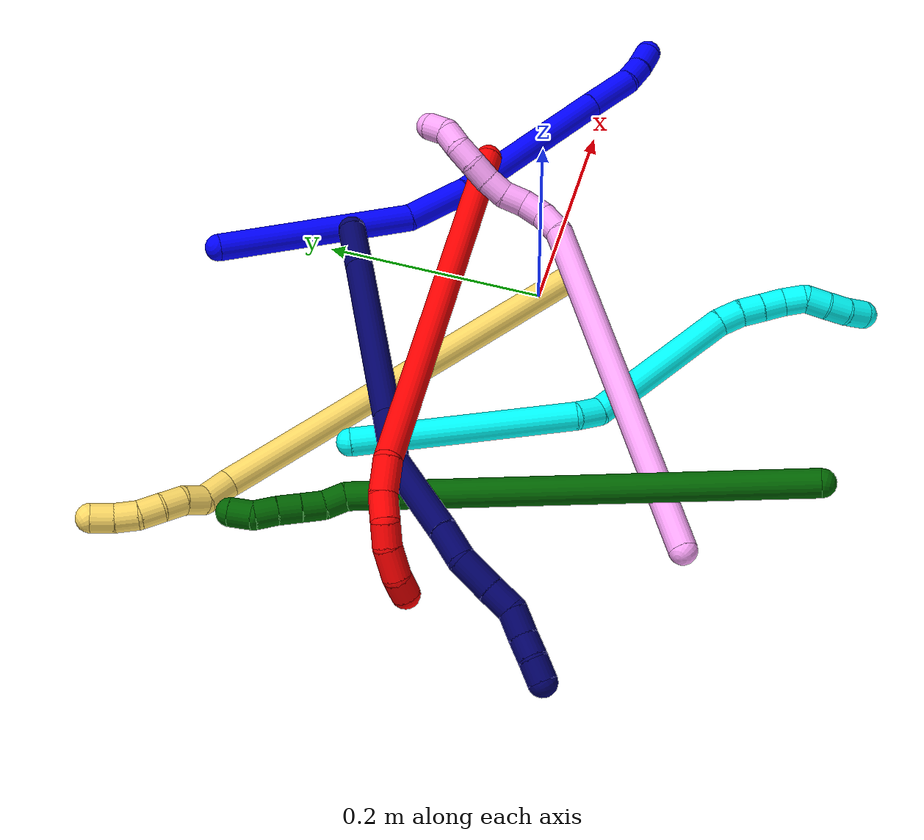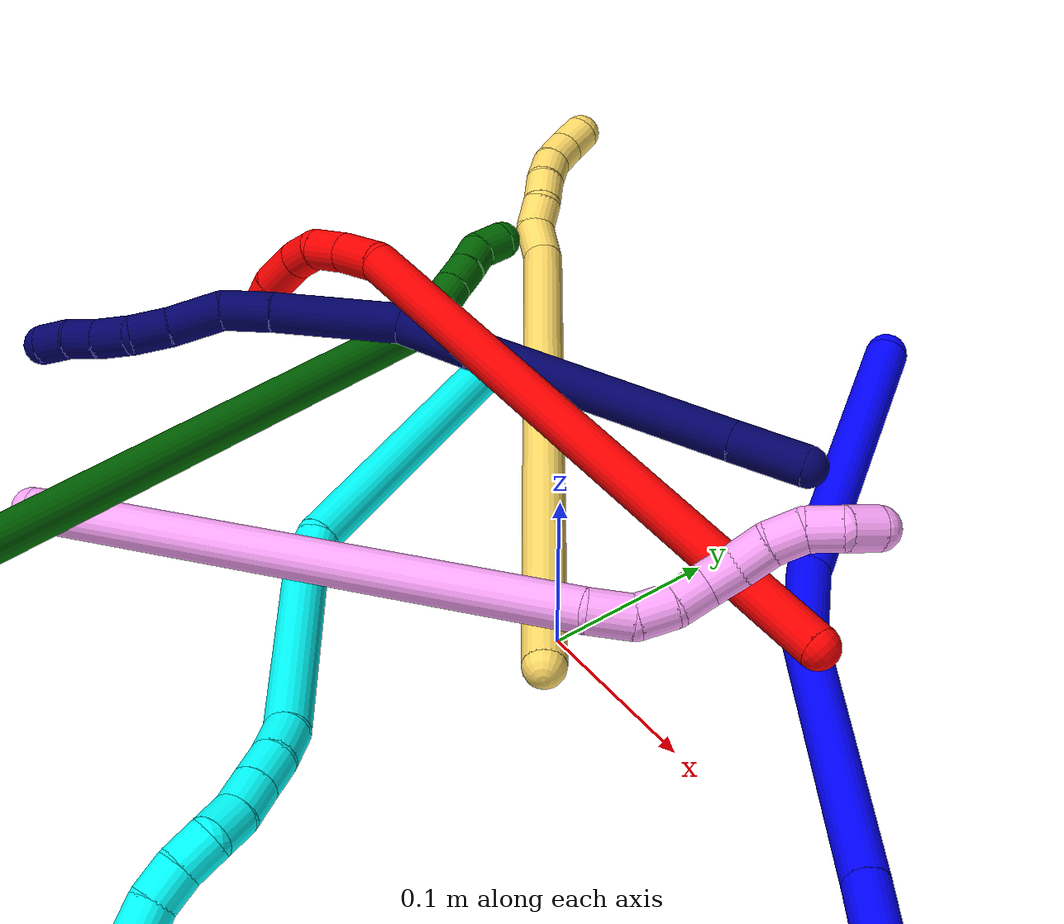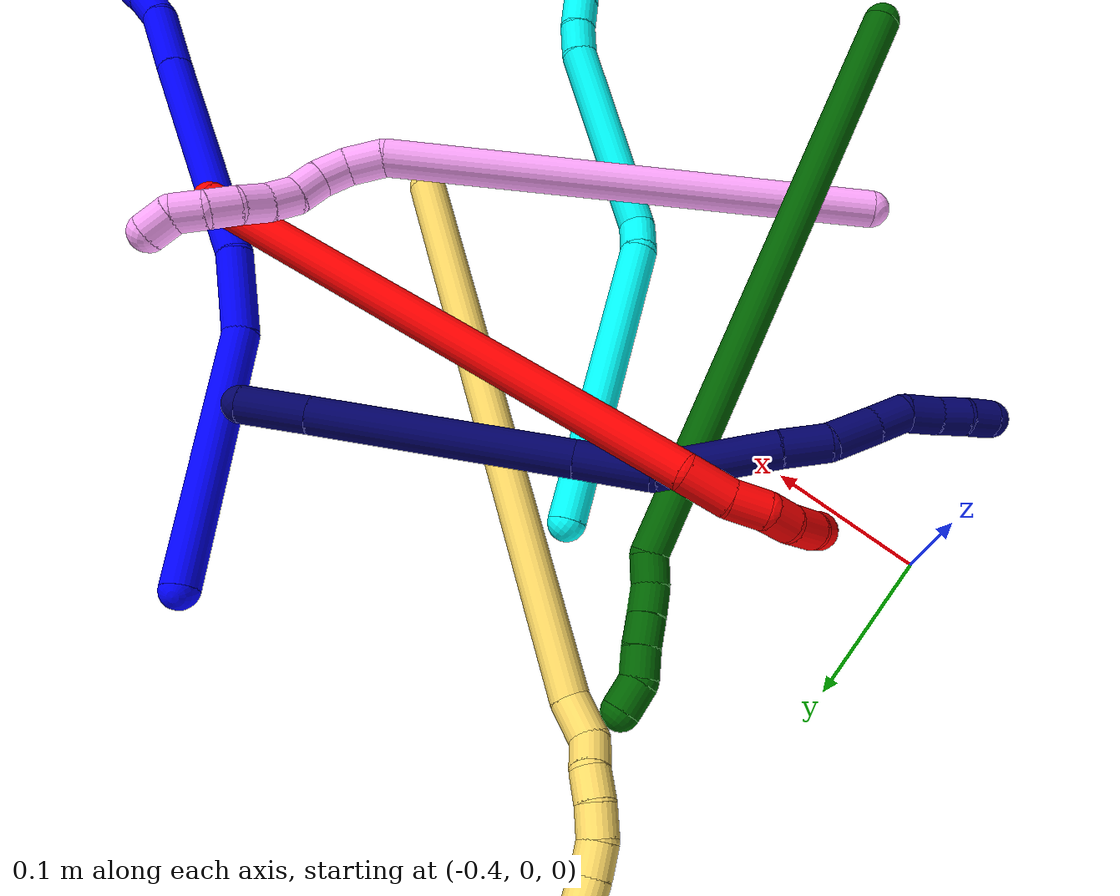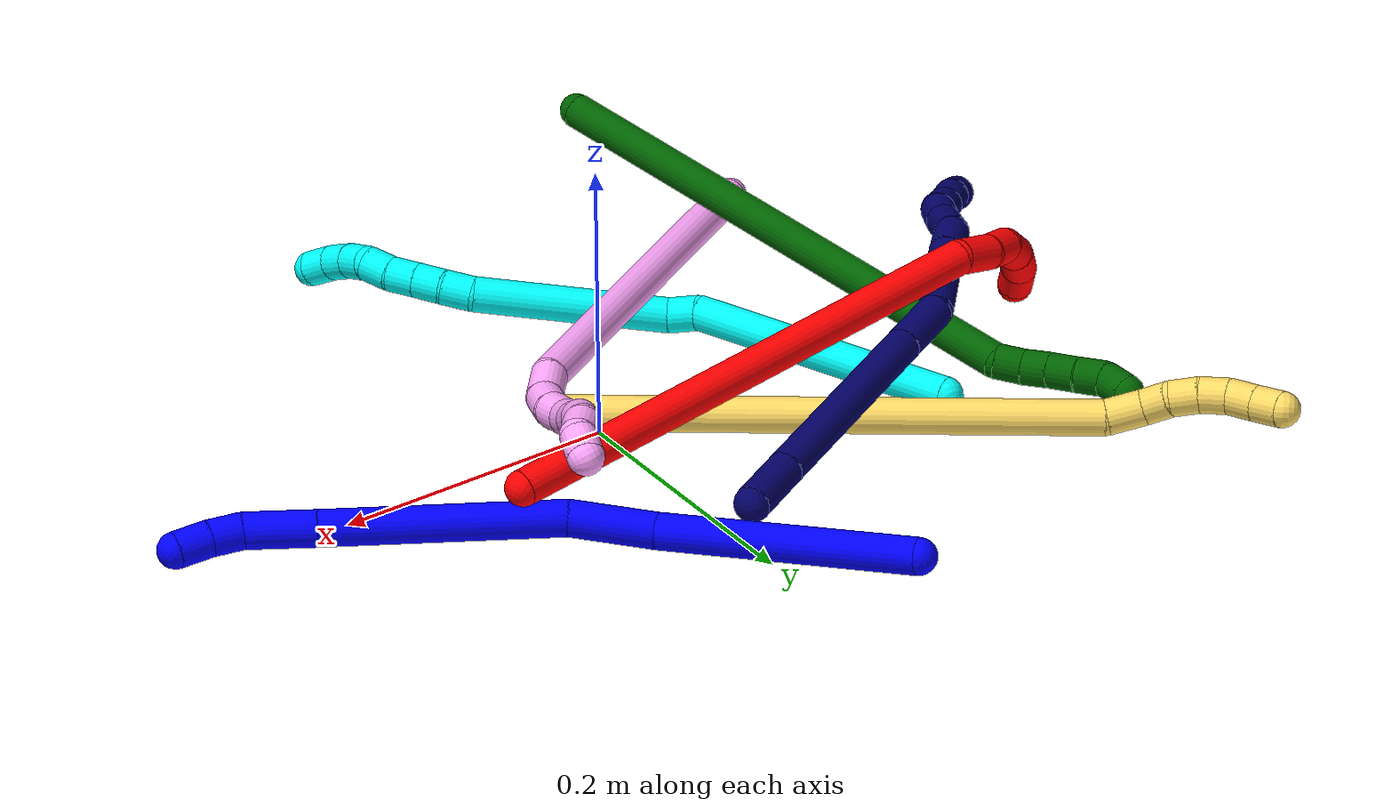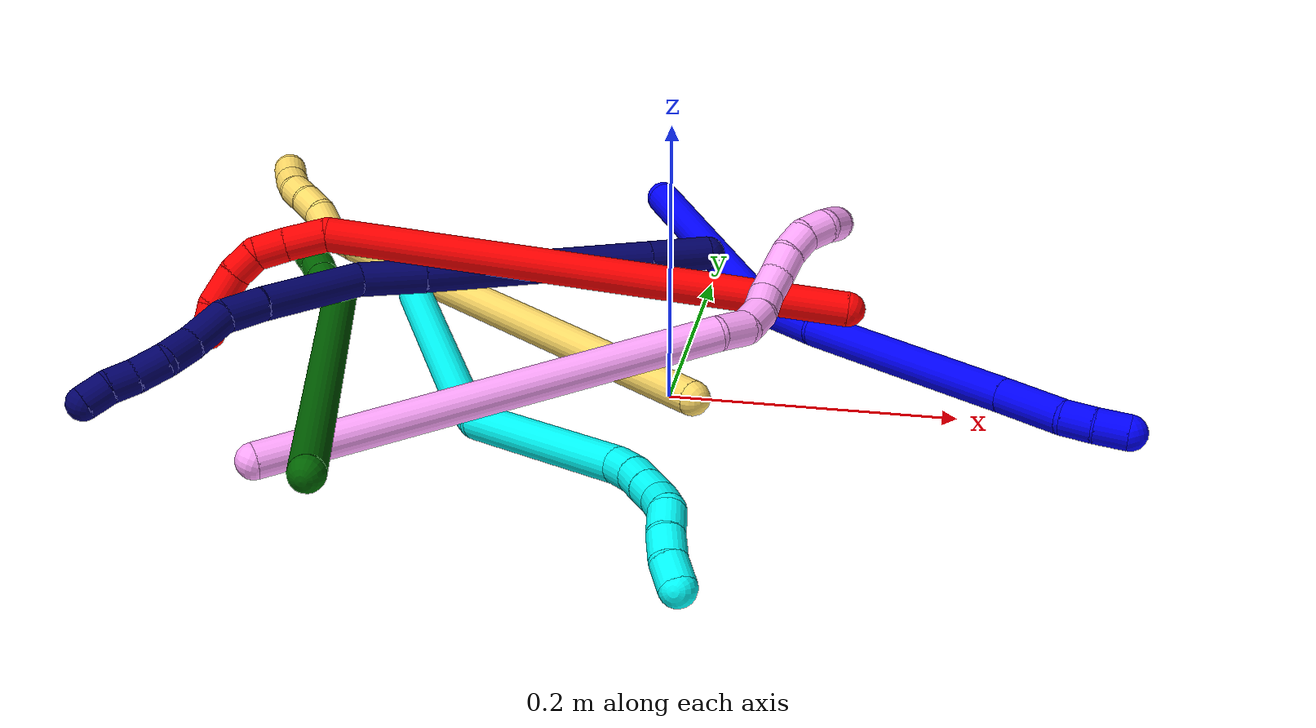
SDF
<sdf version="1.7">
 <world name="default">
  <plugin name="TubeGeneratorPlugin" filename="libtube_generator_plugin.so"/>
  <model name="photoneo_s_sensor">
   <static>1</static>
   <pose>0 0 2 1.57079 1.57079 3.14159</pose>
   <link name="link">
    <inertial><mass>0.1</mass></inertial>
    <sensor name="sensor" type="depth">
     <update_rate>30</update_rate>
     <camera>
      <horizontal_fov>1.22</horizontal_fov>
      <image><width>1920</width><height>1200</height><format>B8G8R8</format></image>
      <clip><near>0.1</near><far>4</far></clip>
      <depth_camera><output>points</output></depth_camera>
     </camera>
     <plugin name="camera_plugin" filename="libgazebo_ros_depth_camera.so">
      <baseline>0.2</baseline>
      <alwaysOn>1</alwaysOn>
      <updateRate>0.0</updateRate>
      <cameraName>camera_ir</cameraName>
      <imageTopicName>/camera/color/image_raw</imageTopicName>
      <cameraInfoTopicName>/camera/color/camera_info</cameraInfoTopicName>
      <depthImageTopicName>/camera/depth/image_raw</depthImageTopicName>
      <depthImageCameraInfoTopicName>/camera/depth/camera_info</depthImageCameraInfoTopicName>
      <pointCloudTopicName>/camera/depth/points</pointCloudTopicName>
      <frameName>fr_optical</frameName>
      <pointCloudCutoff>0.1</pointCloudCutoff>
      <pointCloudCutoffMax>2.0</pointCloudCutoffMax>
      <distortionK1>0</distortionK1>
      <distortionK2>0</distortionK2>
      <distortionK3>0</distortionK3>
      <distortionT1>0</distortionT1>
      <distortionT2>0</distortionT2>
      <CxPrime>0</CxPrime>
      <Cx>0</Cx>
      <Cy>0</Cy>
      <focalLength>0</focalLength>
      <hackBaseline>0</hackBaseline>
     </plugin>
    </sensor>
   </link>
  </model>
  <gravity>0 0 -9.8</gravity>
  <magnetic_field>6e-06 2.3e-05 -4.2e-05</magnetic_field>
  <atmosphere type="adiabatic"/>
  <physics name="default_physics" default="0" type="ode">
   <max_step_size>0.003</max_step_size>
   <real_time_factor>1</real_time_factor>
   <real_time_update_rate>1000</real_time_update_rate>
   <max_contacts>10000</max_contacts>
   <ode>
    <solver>
     <type>quick</type>
     <iters>100</iters>
     <sor>1.3</sor>
     <use_dynamic_moi_rescaling>0</use_dynamic_moi_rescaling>
    </solver>
    <constraints>
     <contact_max_correcting_vel>0</contact_max_correcting_vel>
     <contact_surface_layer>0.001</contact_surface_layer>
     <cfm>0</cfm>
     <erp>0.2</erp>
    </constraints>
   </ode>
  </physics>
  <scene><ambient>0.4 0.4 0.4 1</ambient><background>0.7 0.7 0.7 1</background><shadows>0</shadows></scene>
  <audio><device>default</device></audio>
  <spherical_coordinates>
   <surface_model>EARTH_WGS84</surface_model>
   <latitude_deg>0</latitude_deg>
   <longitude_deg>0</longitude_deg>
   <elevation>0</elevation>
   <heading_deg>0</heading_deg>
  </spherical_coordinates>
  <model name="bin">
   <static>1</static>
   <link name="bottom">
    <collision name="collision-bottom">
     <pose>0 0 -0.01 0 -0 0</pose>
     <geometry><box><size>0.8 0.6 0.02</size></box></geometry>
     <surface>
      <friction><ode><mu>100</mu><mu2>100</mu2></ode></friction>
      <contact><collide_bitmask>65535</collide_bitmask></contact>
     </surface>
    </collision>
   </link>
   <link name="west_wall">
    <collision name="collision-west_wall">
     <pose>-0.41 0 0.1 0 -0 0</pose>
     <geometry><box><size>0.02 0.6 0.2</size></box></geometry>
     <surface>
      <friction><ode><mu>100</mu><mu2>100</mu2></ode></friction>
      <contact><collide_bitmask>65535</collide_bitmask></contact>
     </surface>
    </collision>
   </link>
   <link name="east_wall">
    <collision name="collision-east_wall">
     <pose>0.41 0 0.1 0 -0 0</pose>
     <geometry><box><size>0.02 0.6 0.2</size></box></geometry>
     <surface>
      <friction><ode><mu>100</mu><mu2>100</mu2></ode></friction>
      <contact><collide_bitmask>65535</collide_bitmask></contact>
     </surface>
    </collision>
   </link>
   <link name="south_wall">
    <collision name="collision-south_wall">
     <pose>0 -0.31 0.1 0 -0 0</pose>
     <geometry><box><size>0.8 0.02 0.2</size></box></geometry>
     <surface>
      <friction><ode><mu>100</mu><mu2>100</mu2></ode></friction>
      <contact><collide_bitmask>65535</collide_bitmask></contact>
     </surface>
    </collision>
   </link>
   <link name="north_wall">
    <collision name="collision-north_wall">
     <pose>0 0.31 0.1 0 -0 0</pose>
     <geometry><box><size>0.8 0.02 0.2</size></box></geometry>
     <surface>
      <friction><ode><mu>100</mu><mu2>100</mu2></ode></friction>
      <contact><collide_bitmask>65535</collide_bitmask></contact>
     </surface>
    </collision>
   </link>
  </model>
  <model name="1">
   <static>0</static>
   <link name="1">
    <collision name="collision-cylinder-e_1_1_4">
     <pose>0.022331 -0.06528 -0.058959 2.30536 0.24861 0.548275</pose>
     <geometry><cylinder><radius>0.0125</radius><length>0.181508</length></cylinder></geometry>
     <surface>
      <friction><ode><mu>1.16</mu><mu2>1.16</mu2><slip1>0</slip1><slip2>0</slip2></ode></friction>
      <contact><ode><kp>1e+06</kp><kd>1</kd><max_vel>0</max_vel><min_depth>0.001</min_depth></ode></contact>
     </surface>
    </collision>
    <visual name="visual-cylinder-e_1_1_4">
     <pose>0.022331 -0.06528 -0.058959 2.30536 0.24861 0.548275</pose>
     <geometry><cylinder><radius>0.0125</radius><length>0.181508</length></cylinder></geometry>
     <material><ambient>0 0 1 1</ambient></material>
    </visual>
    <collision name="collision-cylinder-e_2_4_5">
     <pose>0.059158 -0.151987 -0.132573 2.17069 0.509287 0.916696</pose>
     <geometry><cylinder><radius>0.0125</radius><length>0.059465</length></cylinder></geometry>
     <surface>
      <friction><ode><mu>1.16</mu><mu2>1.16</mu2><slip1>0</slip1><slip2>0</slip2></ode></friction>
      <contact><ode><kp>1e+06</kp><kd>1</kd><max_vel>0</max_vel><min_depth>0.001</min_depth></ode></contact>
     </surface>
    </collision>
    <visual name="visual-cylinder-e_2_4_5">
     <pose>0.059158 -0.151987 -0.132573 2.17069 0.509287 0.916696</pose>
     <geometry><cylinder><radius>0.0125</radius><length>0.059465</length></cylinder></geometry>
     <material><ambient>0 0 1 1</ambient></material>
    </visual>
    <collision name="collision-cylinder-e_3_5_6">
     <pose>0.126122 -0.218362 -0.191152 2.34465 0.695647 1.42194</pose>
     <geometry><cylinder><radius>0.0125</radius><length>0.163739</length></cylinder></geometry>
     <surface>
      <friction><ode><mu>1.16</mu><mu2>1.16</mu2><slip1>0</slip1><slip2>0</slip2></ode></friction>
      <contact><ode><kp>1e+06</kp><kd>1</kd><max_vel>0</max_vel><min_depth>0.001</min_depth></ode></contact>
     </surface>
    </collision>
    <visual name="visual-cylinder-e_3_5_6">
     <pose>0.126122 -0.218362 -0.191152 2.34465 0.695647 1.42194</pose>
     <geometry><cylinder><radius>0.0125</radius><length>0.163739</length></cylinder></geometry>
     <material><ambient>0 0 1 1</ambient></material>
    </visual>
    <collision name="collision-cylinder-e_4_6_7">
     <pose>0.193956 -0.277043 -0.248332 2.33861 0.677776 1.38584</pose>
     <geometry><cylinder><radius>0.0125</radius><length>0.049006</length></cylinder></geometry>
     <surface>
      <friction><ode><mu>1.16</mu><mu2>1.16</mu2><slip1>0</slip1><slip2>0</slip2></ode></friction>
      <contact><ode><kp>1e+06</kp><kd>1</kd><max_vel>0</max_vel><min_depth>0.001</min_depth></ode></contact>
     </surface>
    </collision>
    <visual name="visual-cylinder-e_4_6_7">
     <pose>0.193956 -0.277043 -0.248332 2.33861 0.677776 1.38584</pose>
     <geometry><cylinder><radius>0.0125</radius><length>0.049006</length></cylinder></geometry>
     <material><ambient>0 0 1 1</ambient></material>
    </visual>
    <collision name="collision-cylinder-e_5_7_8">
     <pose>0.218266 -0.294428 -0.267357 2.57695 0.91881 2.08096</pose>
     <geometry><cylinder><radius>0.0125</radius><length>0.022506</length></cylinder></geometry>
     <surface>
      <friction><ode><mu>1.16</mu><mu2>1.16</mu2><slip1>0</slip1><slip2>0</slip2></ode></friction>
      <contact><ode><kp>1e+06</kp><kd>1</kd><max_vel>0</max_vel><min_depth>0.001</min_depth></ode></contact>
     </surface>
    </collision>
    <visual name="visual-cylinder-e_5_7_8">
     <pose>0.218266 -0.294428 -0.267357 2.57695 0.91881 2.08096</pose>
     <geometry><cylinder><radius>0.0125</radius><length>0.022506</length></cylinder></geometry>
     <material><ambient>0 0 1 1</ambient></material>
    </visual>
    <collision name="collision-cylinder-e_6_8_2">
     <pose>0.237359 -0.300367 -0.278881 2.76367 1.0229 2.48479</pose>
     <geometry><cylinder><radius>0.0125</radius><length>0.023776</length></cylinder></geometry>
     <surface>
      <friction><ode><mu>1.16</mu><mu2>1.16</mu2><slip1>0</slip1><slip2>0</slip2></ode></friction>
      <contact><ode><kp>1e+06</kp><kd>1</kd><max_vel>0</max_vel><min_depth>0.001</min_depth></ode></contact>
     </surface>
    </collision>
    <visual name="visual-cylinder-e_6_8_2">
     <pose>0.237359 -0.300367 -0.278881 2.76367 1.0229 2.48479</pose>
     <geometry><cylinder><radius>0.0125</radius><length>0.023776</length></cylinder></geometry>
     <material><ambient>0 0 1 1</ambient></material>
    </visual>
    <collision name="collision-sphere-2">
     <pose>0.247506 -0.302652 -0.284636 0 -0 0</pose>
     <geometry><sphere><radius>0.0125</radius></sphere></geometry>
     <surface>
      <friction><ode><mu>1.16</mu><mu2>1.16</mu2><slip1>0</slip1><slip2>0</slip2></ode></friction>
      <contact><ode><kp>1e+06</kp><kd>1</kd><max_vel>0</max_vel><min_depth>0.001</min_depth></ode></contact>
     </surface>
    </collision>
    <visual name="visual-sphere-2">
     <pose>0.247506 -0.302652 -0.284636 0 -0 0</pose>
     <geometry><sphere><radius>0.0125</radius></sphere></geometry>
     <material><ambient>0 0 1 1</ambient></material>
    </visual>
    <collision name="collision-sphere-4">
     <pose>0.044661 -0.13056 -0.117918 0 -0 0</pose>
     <geometry><sphere><radius>0.0125</radius></sphere></geometry>
     <surface>
      <friction><ode><mu>1.16</mu><mu2>1.16</mu2><slip1>0</slip1><slip2>0</slip2></ode></friction>
      <contact><ode><kp>1e+06</kp><kd>1</kd><max_vel>0</max_vel><min_depth>0.001</min_depth></ode></contact>
     </surface>
    </collision>
    <visual name="visual-sphere-4">
     <pose>0.044661 -0.13056 -0.117918 0 -0 0</pose>
     <geometry><sphere><radius>0.0125</radius></sphere></geometry>
     <material><ambient>0 0 1 1</ambient></material>
    </visual>
    <collision name="collision-sphere-1">
     <geometry><sphere><radius>0.0125</radius></sphere></geometry>
     <surface>
      <friction><ode><mu>1.16</mu><mu2>1.16</mu2><slip1>0</slip1><slip2>0</slip2></ode></friction>
      <contact><ode><kp>1e+06</kp><kd>1</kd><max_vel>0</max_vel><min_depth>0.001</min_depth></ode></contact>
     </surface>
    </collision>
    <visual name="visual-sphere-1">
     <geometry><sphere><radius>0.0125</radius></sphere></geometry>
     <material><ambient>0 0 1 1</ambient></material>
    </visual>
    <collision name="collision-sphere-8">
     <pose>0.227211 -0.298082 -0.273125 0 -0 0</pose>
     <geometry><sphere><radius>0.0125</radius></sphere></geometry>
     <surface>
      <friction><ode><mu>1.16</mu><mu2>1.16</mu2><slip1>0</slip1><slip2>0</slip2></ode></friction>
      <contact><ode><kp>1e+06</kp><kd>1</kd><max_vel>0</max_vel><min_depth>0.001</min_depth></ode></contact>
     </surface>
    </collision>
    <visual name="visual-sphere-8">
     <pose>0.227211 -0.298082 -0.273125 0 -0 0</pose>
     <geometry><sphere><radius>0.0125</radius></sphere></geometry>
     <material><ambient>0 0 1 1</ambient></material>
    </visual>
    <collision name="collision-sphere-5">
     <pose>0.073654 -0.173413 -0.147229 0 -0 0</pose>
     <geometry><sphere><radius>0.0125</radius></sphere></geometry>
     <surface>
      <friction><ode><mu>1.16</mu><mu2>1.16</mu2><slip1>0</slip1><slip2>0</slip2></ode></friction>
      <contact><ode><kp>1e+06</kp><kd>1</kd><max_vel>0</max_vel><min_depth>0.001</min_depth></ode></contact>
     </surface>
    </collision>
    <visual name="visual-sphere-5">
     <pose>0.073654 -0.173413 -0.147229 0 -0 0</pose>
     <geometry><sphere><radius>0.0125</radius></sphere></geometry>
     <material><ambient>0 0 1 1</ambient></material>
    </visual>
    <collision name="collision-sphere-6">
     <pose>0.178591 -0.263311 -0.235074 0 -0 0</pose>
     <geometry><sphere><radius>0.0125</radius></sphere></geometry>
     <surface>
      <friction><ode><mu>1.16</mu><mu2>1.16</mu2><slip1>0</slip1><slip2>0</slip2></ode></friction>
      <contact><ode><kp>1e+06</kp><kd>1</kd><max_vel>0</max_vel><min_depth>0.001</min_depth></ode></contact>
     </surface>
    </collision>
    <visual name="visual-sphere-6">
     <pose>0.178591 -0.263311 -0.235074 0 -0 0</pose>
     <geometry><sphere><radius>0.0125</radius></sphere></geometry>
     <material><ambient>0 0 1 1</ambient></material>
    </visual>
    <collision name="collision-sphere-7">
     <pose>0.209321 -0.290775 -0.261589 0 -0 0</pose>
     <geometry><sphere><radius>0.0125</radius></sphere></geometry>
     <surface>
      <friction><ode><mu>1.16</mu><mu2>1.16</mu2><slip1>0</slip1><slip2>0</slip2></ode></friction>
      <contact><ode><kp>1e+06</kp><kd>1</kd><max_vel>0</max_vel><min_depth>0.001</min_depth></ode></contact>
     </surface>
    </collision>
    <visual name="visual-sphere-7">
     <pose>0.209321 -0.290775 -0.261589 0 -0 0</pose>
     <geometry><sphere><radius>0.0125</radius></sphere></geometry>
     <material><ambient>0 0 1 1</ambient></material>
    </visual>
    <inertial>
     <pose>0.096566 -0.167972 -0.149403 0 -0 0</pose>
     <mass>0.5</mass>
     <inertia>
      <ixx>0.001053</ixx>
      <ixy>0</ixy>
      <ixz>0</ixz>
      <iyy>0.000434</iyy>
      <iyz>0</iyz>
      <izz>0.000184</izz>
     </inertia>
    </inertial>
   </link>
   <pose>-0.05213 0.288507 0.033532 -0.533135 -0.26988 0.292147</pose>
  </model>
  <model name="2">
   <static>0</static>
   <link name="2">
    <collision name="collision-cylinder-e_1_1_4">
     <pose>-0.095447 -0.019869 -0.161637 3.01928 -0.530127 -2.69788</pose>
     <geometry><cylinder><radius>0.0125</radius><length>0.377526</length></cylinder></geometry>
     <surface>
      <friction><ode><mu>1.16</mu><mu2>1.16</mu2><slip1>0</slip1><slip2>0</slip2></ode></friction>
      <contact><ode><kp>1e+06</kp><kd>1</kd><max_vel>0</max_vel><min_depth>0.001</min_depth></ode></contact>
     </surface>
    </collision>
    <visual name="visual-cylinder-e_1_1_4">
     <pose>-0.095447 -0.019869 -0.161637 3.01928 -0.530127 -2.69788</pose>
     <geometry><cylinder><radius>0.0125</radius><length>0.377526</length></cylinder></geometry>
     <material><ambient>1 0 0 1</ambient></material>
    </visual>
    <collision name="collision-cylinder-e_2_4_5">
     <pose>-0.202606 -0.03852 -0.333355 -3.02144 -0.856577 2.87962</pose>
     <geometry><cylinder><radius>0.0125</radius><length>0.031002</length></cylinder></geometry>
     <surface>
      <friction><ode><mu>1.16</mu><mu2>1.16</mu2><slip1>0</slip1><slip2>0</slip2></ode></friction>
      <contact><ode><kp>1e+06</kp><kd>1</kd><max_vel>0</max_vel><min_depth>0.001</min_depth></ode></contact>
     </surface>
    </collision>
    <visual name="visual-cylinder-e_2_4_5">
     <pose>-0.202606 -0.03852 -0.333355 -3.02144 -0.856577 2.87962</pose>
     <geometry><cylinder><radius>0.0125</radius><length>0.031002</length></cylinder></geometry>
     <material><ambient>1 0 0 1</ambient></material>
    </visual>
    <collision name="collision-cylinder-e_3_5_6">
     <pose>-0.222318 -0.034117 -0.351203 -2.75236 -0.761257 2.22617</pose>
     <geometry><cylinder><radius>0.0125</radius><length>0.023195</length></cylinder></geometry>
     <surface>
      <friction><ode><mu>1.16</mu><mu2>1.16</mu2><slip1>0</slip1><slip2>0</slip2></ode></friction>
      <contact><ode><kp>1e+06</kp><kd>1</kd><max_vel>0</max_vel><min_depth>0.001</min_depth></ode></contact>
     </surface>
    </collision>
    <visual name="visual-cylinder-e_3_5_6">
     <pose>-0.222318 -0.034117 -0.351203 -2.75236 -0.761257 2.22617</pose>
     <geometry><cylinder><radius>0.0125</radius><length>0.023195</length></cylinder></geometry>
     <material><ambient>1 0 0 1</ambient></material>
    </visual>
    <collision name="collision-cylinder-e_4_6_7">
     <pose>-0.239754 -0.02749 -0.361431 -2.1913 -1.14935 1.79893</pose>
     <geometry><cylinder><radius>0.0125</radius><length>0.02068</length></cylinder></geometry>
     <surface>
      <friction><ode><mu>1.16</mu><mu2>1.16</mu2><slip1>0</slip1><slip2>0</slip2></ode></friction>
      <contact><ode><kp>1e+06</kp><kd>1</kd><max_vel>0</max_vel><min_depth>0.001</min_depth></ode></contact>
     </surface>
    </collision>
    <visual name="visual-cylinder-e_4_6_7">
     <pose>-0.239754 -0.02749 -0.361431 -2.1913 -1.14935 1.79893</pose>
     <geometry><cylinder><radius>0.0125</radius><length>0.02068</length></cylinder></geometry>
     <material><ambient>1 0 0 1</ambient></material>
    </visual>
    <collision name="collision-cylinder-e_5_7_8">
     <pose>-0.26088 -0.017034 -0.364435 -1.64823 -1.02904 1.09674</pose>
     <geometry><cylinder><radius>0.0125</radius><length>0.027288</length></cylinder></geometry>
     <surface>
      <friction><ode><mu>1.16</mu><mu2>1.16</mu2><slip1>0</slip1><slip2>0</slip2></ode></friction>
      <contact><ode><kp>1e+06</kp><kd>1</kd><max_vel>0</max_vel><min_depth>0.001</min_depth></ode></contact>
     </surface>
    </collision>
    <visual name="visual-cylinder-e_5_7_8">
     <pose>-0.26088 -0.017034 -0.364435 -1.64823 -1.02904 1.09674</pose>
     <geometry><cylinder><radius>0.0125</radius><length>0.027288</length></cylinder></geometry>
     <material><ambient>1 0 0 1</ambient></material>
    </visual>
    <collision name="collision-cylinder-e_6_8_2">
     <pose>-0.280403 -0.004183 -0.362206 -1.12727 -0.881058 0.579158</pose>
     <geometry><cylinder><radius>0.0125</radius><length>0.020309</length></cylinder></geometry>
     <surface>
      <friction><ode><mu>1.16</mu><mu2>1.16</mu2><slip1>0</slip1><slip2>0</slip2></ode></friction>
      <contact><ode><kp>1e+06</kp><kd>1</kd><max_vel>0</max_vel><min_depth>0.001</min_depth></ode></contact>
     </surface>
    </collision>
    <visual name="visual-cylinder-e_6_8_2">
     <pose>-0.280403 -0.004183 -0.362206 -1.12727 -0.881058 0.579158</pose>
     <geometry><cylinder><radius>0.0125</radius><length>0.020309</length></cylinder></geometry>
     <material><ambient>1 0 0 1</ambient></material>
    </visual>
    <collision name="collision-sphere-2">
     <pose>-0.288237 0.001654 -0.359433 0 -0 0</pose>
     <geometry><sphere><radius>0.0125</radius></sphere></geometry>
     <surface>
      <friction><ode><mu>1.16</mu><mu2>1.16</mu2><slip1>0</slip1><slip2>0</slip2></ode></friction>
      <contact><ode><kp>1e+06</kp><kd>1</kd><max_vel>0</max_vel><min_depth>0.001</min_depth></ode></contact>
     </surface>
    </collision>
    <visual name="visual-sphere-2">
     <pose>-0.288237 0.001654 -0.359433 0 -0 0</pose>
     <geometry><sphere><radius>0.0125</radius></sphere></geometry>
     <material><ambient>1 0 0 1</ambient></material>
    </visual>
    <collision name="collision-sphere-4">
     <pose>-0.190893 -0.039737 -0.323275 0 -0 0</pose>
     <geometry><sphere><radius>0.0125</radius></sphere></geometry>
     <surface>
      <friction><ode><mu>1.16</mu><mu2>1.16</mu2><slip1>0</slip1><slip2>0</slip2></ode></friction>
      <contact><ode><kp>1e+06</kp><kd>1</kd><max_vel>0</max_vel><min_depth>0.001</min_depth></ode></contact>
     </surface>
    </collision>
    <visual name="visual-sphere-4">
     <pose>-0.190893 -0.039737 -0.323275 0 -0 0</pose>
     <geometry><sphere><radius>0.0125</radius></sphere></geometry>
     <material><ambient>1 0 0 1</ambient></material>
    </visual>
    <collision name="collision-sphere-1">
     <geometry><sphere><radius>0.0125</radius></sphere></geometry>
     <surface>
      <friction><ode><mu>1.16</mu><mu2>1.16</mu2><slip1>0</slip1><slip2>0</slip2></ode></friction>
      <contact><ode><kp>1e+06</kp><kd>1</kd><max_vel>0</max_vel><min_depth>0.001</min_depth></ode></contact>
     </surface>
    </collision>
    <visual name="visual-sphere-1">
     <geometry><sphere><radius>0.0125</radius></sphere></geometry>
     <material><ambient>1 0 0 1</ambient></material>
    </visual>
    <collision name="collision-sphere-8">
     <pose>-0.27257 -0.010019 -0.364979 0 -0 0</pose>
     <geometry><sphere><radius>0.0125</radius></sphere></geometry>
     <surface>
      <friction><ode><mu>1.16</mu><mu2>1.16</mu2><slip1>0</slip1><slip2>0</slip2></ode></friction>
      <contact><ode><kp>1e+06</kp><kd>1</kd><max_vel>0</max_vel><min_depth>0.001</min_depth></ode></contact>
     </surface>
    </collision>
    <visual name="visual-sphere-8">
     <pose>-0.27257 -0.010019 -0.364979 0 -0 0</pose>
     <geometry><sphere><radius>0.0125</radius></sphere></geometry>
     <material><ambient>1 0 0 1</ambient></material>
    </visual>
    <collision name="collision-sphere-5">
     <pose>-0.214318 -0.037303 -0.343435 0 -0 0</pose>
     <geometry><sphere><radius>0.0125</radius></sphere></geometry>
     <surface>
      <friction><ode><mu>1.16</mu><mu2>1.16</mu2><slip1>0</slip1><slip2>0</slip2></ode></friction>
      <contact><ode><kp>1e+06</kp><kd>1</kd><max_vel>0</max_vel><min_depth>0.001</min_depth></ode></contact>
     </surface>
    </collision>
    <visual name="visual-sphere-5">
     <pose>-0.214318 -0.037303 -0.343435 0 -0 0</pose>
     <geometry><sphere><radius>0.0125</radius></sphere></geometry>
     <material><ambient>1 0 0 1</ambient></material>
    </visual>
    <collision name="collision-sphere-6">
     <pose>-0.230319 -0.030931 -0.358972 0 -0 0</pose>
     <geometry><sphere><radius>0.0125</radius></sphere></geometry>
     <surface>
      <friction><ode><mu>1.16</mu><mu2>1.16</mu2><slip1>0</slip1><slip2>0</slip2></ode></friction>
      <contact><ode><kp>1e+06</kp><kd>1</kd><max_vel>0</max_vel><min_depth>0.001</min_depth></ode></contact>
     </surface>
    </collision>
    <visual name="visual-sphere-6">
     <pose>-0.230319 -0.030931 -0.358972 0 -0 0</pose>
     <geometry><sphere><radius>0.0125</radius></sphere></geometry>
     <material><ambient>1 0 0 1</ambient></material>
    </visual>
    <collision name="collision-sphere-7">
     <pose>-0.24919 -0.024048 -0.363891 0 -0 0</pose>
     <geometry><sphere><radius>0.0125</radius></sphere></geometry>
     <surface>
      <friction><ode><mu>1.16</mu><mu2>1.16</mu2><slip1>0</slip1><slip2>0</slip2></ode></friction>
      <contact><ode><kp>1e+06</kp><kd>1</kd><max_vel>0</max_vel><min_depth>0.001</min_depth></ode></contact>
     </surface>
    </collision>
    <visual name="visual-sphere-7">
     <pose>-0.24919 -0.024048 -0.363891 0 -0 0</pose>
     <geometry><sphere><radius>0.0125</radius></sphere></geometry>
     <material><ambient>1 0 0 1</ambient></material>
    </visual>
    <inertial>
     <pose>-0.130486 -0.02121 -0.208557 0 -0 0</pose>
     <mass>0.5</mass>
     <inertia>
      <ixx>-0.005192</ixx>
      <ixy>0</ixy>
      <ixz>0</ixz>
      <iyy>0.002499</iyy>
      <iyz>0</iyz>
      <izz>0.002726</izz>
     </inertia>
    </inertial>
   </link>
   <pose>0.114908 0.08169 0.040193 -2.74317 -0.91797 -0.177213</pose>
  </model>
  <model name="3">
   <static>0</static>
   <link name="3">
    <collision name="collision-cylinder-e_1_1_4">
     <pose>0.026673 -0.045091 0.083396 0.495665 0.274261 0.069807</pose>
     <geometry><cylinder><radius>0.0125</radius><length>0.196972</length></cylinder></geometry>
     <surface>
      <friction><ode><mu>1.16</mu><mu2>1.16</mu2><slip1>0</slip1><slip2>0</slip2></ode></friction>
      <contact><ode><kp>1e+06</kp><kd>1</kd><max_vel>0</max_vel><min_depth>0.001</min_depth></ode></contact>
     </surface>
    </collision>
    <visual name="visual-cylinder-e_1_1_4">
     <pose>0.026673 -0.045091 0.083396 0.495665 0.274261 0.069807</pose>
     <geometry><cylinder><radius>0.0125</radius><length>0.196972</length></cylinder></geometry>
     <material><ambient>0.003922 1 0.996078 1</ambient></material>
    </visual>
    <collision name="collision-cylinder-e_2_4_5">
     <pose>0.05732 -0.098474 0.173483 0.891786 0.356904 0.172009</pose>
     <geometry><cylinder><radius>0.0125</radius><length>0.022744</length></cylinder></geometry>
     <surface>
      <friction><ode><mu>1.16</mu><mu2>1.16</mu2><slip1>0</slip1><slip2>0</slip2></ode></friction>
      <contact><ode><kp>1e+06</kp><kd>1</kd><max_vel>0</max_vel><min_depth>0.001</min_depth></ode></contact>
     </surface>
    </collision>
    <visual name="visual-cylinder-e_2_4_5">
     <pose>0.05732 -0.098474 0.173483 0.891786 0.356904 0.172009</pose>
     <geometry><cylinder><radius>0.0125</radius><length>0.022744</length></cylinder></geometry>
     <material><ambient>0.003922 1 0.996078 1</ambient></material>
    </visual>
    <collision name="collision-cylinder-e_3_5_6">
     <pose>0.109946 -0.139719 0.216183 0.741118 0.78377 0.318391</pose>
     <geometry><cylinder><radius>0.0125</radius><length>0.137835</length></cylinder></geometry>
     <surface>
      <friction><ode><mu>1.16</mu><mu2>1.16</mu2><slip1>0</slip1><slip2>0</slip2></ode></friction>
      <contact><ode><kp>1e+06</kp><kd>1</kd><max_vel>0</max_vel><min_depth>0.001</min_depth></ode></contact>
     </surface>
    </collision>
    <visual name="visual-cylinder-e_3_5_6">
     <pose>0.109946 -0.139719 0.216183 0.741118 0.78377 0.318391</pose>
     <geometry><cylinder><radius>0.0125</radius><length>0.137835</length></cylinder></geometry>
     <material><ambient>0.003922 1 0.996078 1</ambient></material>
    </visual>
    <collision name="collision-cylinder-e_4_6_7">
     <pose>0.164535 -0.17755 0.259741 0.573742 0.583681 0.17679</pose>
     <geometry><cylinder><radius>0.0125</radius><length>0.021543</length></cylinder></geometry>
     <surface>
      <friction><ode><mu>1.16</mu><mu2>1.16</mu2><slip1>0</slip1><slip2>0</slip2></ode></friction>
      <contact><ode><kp>1e+06</kp><kd>1</kd><max_vel>0</max_vel><min_depth>0.001</min_depth></ode></contact>
     </surface>
    </collision>
    <visual name="visual-cylinder-e_4_6_7">
     <pose>0.164535 -0.17755 0.259741 0.573742 0.583681 0.17679</pose>
     <geometry><cylinder><radius>0.0125</radius><length>0.021543</length></cylinder></geometry>
     <material><ambient>0.003922 1 0.996078 1</ambient></material>
    </visual>
    <collision name="collision-cylinder-e_5_7_8">
     <pose>0.174546 -0.187333 0.275202 0.554841 0.412697 0.119077</pose>
     <geometry><cylinder><radius>0.0125</radius><length>0.020322</length></cylinder></geometry>
     <surface>
      <friction><ode><mu>1.16</mu><mu2>1.16</mu2><slip1>0</slip1><slip2>0</slip2></ode></friction>
      <contact><ode><kp>1e+06</kp><kd>1</kd><max_vel>0</max_vel><min_depth>0.001</min_depth></ode></contact>
     </surface>
    </collision>
    <visual name="visual-cylinder-e_5_7_8">
     <pose>0.174546 -0.187333 0.275202 0.554841 0.412697 0.119077</pose>
     <geometry><cylinder><radius>0.0125</radius><length>0.020322</length></cylinder></geometry>
     <material><ambient>0.003922 1 0.996078 1</ambient></material>
    </visual>
    <collision name="collision-cylinder-e_6_8_9">
     <pose>0.182771 -0.19728 0.290972 0.570597 0.418103 0.124287</pose>
     <geometry><cylinder><radius>0.0125</radius><length>0.020437</length></cylinder></geometry>
     <surface>
      <friction><ode><mu>1.16</mu><mu2>1.16</mu2><slip1>0</slip1><slip2>0</slip2></ode></friction>
      <contact><ode><kp>1e+06</kp><kd>1</kd><max_vel>0</max_vel><min_depth>0.001</min_depth></ode></contact>
     </surface>
    </collision>
    <visual name="visual-cylinder-e_6_8_9">
     <pose>0.182771 -0.19728 0.290972 0.570597 0.418103 0.124287</pose>
     <geometry><cylinder><radius>0.0125</radius><length>0.020437</length></cylinder></geometry>
     <material><ambient>0.003922 1 0.996078 1</ambient></material>
    </visual>
    <collision name="collision-cylinder-e_7_9_10">
     <pose>0.190005 -0.206052 0.307594 0.402277 0.313289 0.064384</pose>
     <geometry><cylinder><radius>0.0125</radius><length>0.02002</length></cylinder></geometry>
     <surface>
      <friction><ode><mu>1.16</mu><mu2>1.16</mu2><slip1>0</slip1><slip2>0</slip2></ode></friction>
      <contact><ode><kp>1e+06</kp><kd>1</kd><max_vel>0</max_vel><min_depth>0.001</min_depth></ode></contact>
     </surface>
    </collision>
    <visual name="visual-cylinder-e_7_9_10">
     <pose>0.190005 -0.206052 0.307594 0.402277 0.313289 0.064384</pose>
     <geometry><cylinder><radius>0.0125</radius><length>0.02002</length></cylinder></geometry>
     <material><ambient>0.003922 1 0.996078 1</ambient></material>
    </visual>
    <collision name="collision-cylinder-e_8_10_11">
     <pose>0.191738 -0.215721 0.32434 0.639678 -0.13502 -0.044781</pose>
     <geometry><cylinder><radius>0.0125</radius><length>0.020085</length></cylinder></geometry>
     <surface>
      <friction><ode><mu>1.16</mu><mu2>1.16</mu2><slip1>0</slip1><slip2>0</slip2></ode></friction>
      <contact><ode><kp>1e+06</kp><kd>1</kd><max_vel>0</max_vel><min_depth>0.001</min_depth></ode></contact>
     </surface>
    </collision>
    <visual name="visual-cylinder-e_8_10_11">
     <pose>0.191738 -0.215721 0.32434 0.639678 -0.13502 -0.044781</pose>
     <geometry><cylinder><radius>0.0125</radius><length>0.020085</length></cylinder></geometry>
     <material><ambient>0.003922 1 0.996078 1</ambient></material>
    </visual>
    <collision name="collision-cylinder-e_9_11_12">
     <pose>0.189565 -0.228803 0.339286 0.798091 -0.082126 -0.034646</pose>
     <geometry><cylinder><radius>0.0125</radius><length>0.020015</length></cylinder></geometry>
     <surface>
      <friction><ode><mu>1.16</mu><mu2>1.16</mu2><slip1>0</slip1><slip2>0</slip2></ode></friction>
      <contact><ode><kp>1e+06</kp><kd>1</kd><max_vel>0</max_vel><min_depth>0.001</min_depth></ode></contact>
     </surface>
    </collision>
    <visual name="visual-cylinder-e_9_11_12">
     <pose>0.189565 -0.228803 0.339286 0.798091 -0.082126 -0.034646</pose>
     <geometry><cylinder><radius>0.0125</radius><length>0.020015</length></cylinder></geometry>
     <material><ambient>0.003922 1 0.996078 1</ambient></material>
    </visual>
    <collision name="collision-cylinder-e_10_12_2">
     <pose>0.189357 -0.244184 0.351905 0.96928 0.061275 0.03227</pose>
     <geometry><cylinder><radius>0.0125</radius><length>0.020027</length></cylinder></geometry>
     <surface>
      <friction><ode><mu>1.16</mu><mu2>1.16</mu2><slip1>0</slip1><slip2>0</slip2></ode></friction>
      <contact><ode><kp>1e+06</kp><kd>1</kd><max_vel>0</max_vel><min_depth>0.001</min_depth></ode></contact>
     </surface>
    </collision>
    <visual name="visual-cylinder-e_10_12_2">
     <pose>0.189357 -0.244184 0.351905 0.96928 0.061275 0.03227</pose>
     <geometry><cylinder><radius>0.0125</radius><length>0.020027</length></cylinder></geometry>
     <material><ambient>0.003922 1 0.996078 1</ambient></material>
    </visual>
    <collision name="collision-sphere-2">
     <pose>0.18997 -0.252425 0.357561 0 -0 0</pose>
     <geometry><sphere><radius>0.0125</radius></sphere></geometry>
     <surface>
      <friction><ode><mu>1.16</mu><mu2>1.16</mu2><slip1>0</slip1><slip2>0</slip2></ode></friction>
      <contact><ode><kp>1e+06</kp><kd>1</kd><max_vel>0</max_vel><min_depth>0.001</min_depth></ode></contact>
     </surface>
    </collision>
    <visual name="visual-sphere-2">
     <pose>0.18997 -0.252425 0.357561 0 -0 0</pose>
     <geometry><sphere><radius>0.0125</radius></sphere></geometry>
     <material><ambient>0.003922 1 0.996078 1</ambient></material>
    </visual>
    <collision name="collision-sphere-12">
     <pose>0.188744 -0.235944 0.346249 0 -0 0</pose>
     <geometry><sphere><radius>0.0125</radius></sphere></geometry>
     <surface>
      <friction><ode><mu>1.16</mu><mu2>1.16</mu2><slip1>0</slip1><slip2>0</slip2></ode></friction>
      <contact><ode><kp>1e+06</kp><kd>1</kd><max_vel>0</max_vel><min_depth>0.001</min_depth></ode></contact>
     </surface>
    </collision>
    <visual name="visual-sphere-12">
     <pose>0.188744 -0.235944 0.346249 0 -0 0</pose>
     <geometry><sphere><radius>0.0125</radius></sphere></geometry>
     <material><ambient>0.003922 1 0.996078 1</ambient></material>
    </visual>
    <collision name="collision-sphere-11">
     <pose>0.190386 -0.221661 0.332324 0 -0 0</pose>
     <geometry><sphere><radius>0.0125</radius></sphere></geometry>
     <surface>
      <friction><ode><mu>1.16</mu><mu2>1.16</mu2><slip1>0</slip1><slip2>0</slip2></ode></friction>
      <contact><ode><kp>1e+06</kp><kd>1</kd><max_vel>0</max_vel><min_depth>0.001</min_depth></ode></contact>
     </surface>
    </collision>
    <visual name="visual-sphere-11">
     <pose>0.190386 -0.221661 0.332324 0 -0 0</pose>
     <geometry><sphere><radius>0.0125</radius></sphere></geometry>
     <material><ambient>0.003922 1 0.996078 1</ambient></material>
    </visual>
    <collision name="collision-sphere-10">
     <pose>0.19309 -0.209781 0.316356 0 -0 0</pose>
     <geometry><sphere><radius>0.0125</radius></sphere></geometry>
     <surface>
      <friction><ode><mu>1.16</mu><mu2>1.16</mu2><slip1>0</slip1><slip2>0</slip2></ode></friction>
      <contact><ode><kp>1e+06</kp><kd>1</kd><max_vel>0</max_vel><min_depth>0.001</min_depth></ode></contact>
     </surface>
    </collision>
    <visual name="visual-sphere-10">
     <pose>0.19309 -0.209781 0.316356 0 -0 0</pose>
     <geometry><sphere><radius>0.0125</radius></sphere></geometry>
     <material><ambient>0.003922 1 0.996078 1</ambient></material>
    </visual>
    <collision name="collision-sphere-9">
     <pose>0.18692 -0.202324 0.298831 0 -0 0</pose>
     <geometry><sphere><radius>0.0125</radius></sphere></geometry>
     <surface>
      <friction><ode><mu>1.16</mu><mu2>1.16</mu2><slip1>0</slip1><slip2>0</slip2></ode></friction>
      <contact><ode><kp>1e+06</kp><kd>1</kd><max_vel>0</max_vel><min_depth>0.001</min_depth></ode></contact>
     </surface>
    </collision>
    <visual name="visual-sphere-9">
     <pose>0.18692 -0.202324 0.298831 0 -0 0</pose>
     <geometry><sphere><radius>0.0125</radius></sphere></geometry>
     <material><ambient>0.003922 1 0.996078 1</ambient></material>
    </visual>
    <collision name="collision-sphere-4">
     <pose>0.053347 -0.090182 0.166791 0 -0 0</pose>
     <geometry><sphere><radius>0.0125</radius></sphere></geometry>
     <surface>
      <friction><ode><mu>1.16</mu><mu2>1.16</mu2><slip1>0</slip1><slip2>0</slip2></ode></friction>
      <contact><ode><kp>1e+06</kp><kd>1</kd><max_vel>0</max_vel><min_depth>0.001</min_depth></ode></contact>
     </surface>
    </collision>
    <visual name="visual-sphere-4">
     <pose>0.053347 -0.090182 0.166791 0 -0 0</pose>
     <geometry><sphere><radius>0.0125</radius></sphere></geometry>
     <material><ambient>0.003922 1 0.996078 1</ambient></material>
    </visual>
    <collision name="collision-sphere-1">
     <geometry><sphere><radius>0.0125</radius></sphere></geometry>
     <surface>
      <friction><ode><mu>1.16</mu><mu2>1.16</mu2><slip1>0</slip1><slip2>0</slip2></ode></friction>
      <contact><ode><kp>1e+06</kp><kd>1</kd><max_vel>0</max_vel><min_depth>0.001</min_depth></ode></contact>
     </surface>
    </collision>
    <visual name="visual-sphere-1">
     <geometry><sphere><radius>0.0125</radius></sphere></geometry>
     <material><ambient>0.003922 1 0.996078 1</ambient></material>
    </visual>
    <collision name="collision-sphere-8">
     <pose>0.178622 -0.192236 0.283114 0 -0 0</pose>
     <geometry><sphere><radius>0.0125</radius></sphere></geometry>
     <surface>
      <friction><ode><mu>1.16</mu><mu2>1.16</mu2><slip1>0</slip1><slip2>0</slip2></ode></friction>
      <contact><ode><kp>1e+06</kp><kd>1</kd><max_vel>0</max_vel><min_depth>0.001</min_depth></ode></contact>
     </surface>
    </collision>
    <visual name="visual-sphere-8">
     <pose>0.178622 -0.192236 0.283114 0 -0 0</pose>
     <geometry><sphere><radius>0.0125</radius></sphere></geometry>
     <material><ambient>0.003922 1 0.996078 1</ambient></material>
    </visual>
    <collision name="collision-sphere-5">
     <pose>0.061293 -0.106765 0.180175 0 -0 0</pose>
     <geometry><sphere><radius>0.0125</radius></sphere></geometry>
     <surface>
      <friction><ode><mu>1.16</mu><mu2>1.16</mu2><slip1>0</slip1><slip2>0</slip2></ode></friction>
      <contact><ode><kp>1e+06</kp><kd>1</kd><max_vel>0</max_vel><min_depth>0.001</min_depth></ode></contact>
     </surface>
    </collision>
    <visual name="visual-sphere-5">
     <pose>0.061293 -0.106765 0.180175 0 -0 0</pose>
     <geometry><sphere><radius>0.0125</radius></sphere></geometry>
     <material><ambient>0.003922 1 0.996078 1</ambient></material>
    </visual>
    <collision name="collision-sphere-6">
     <pose>0.158599 -0.172672 0.252192 0 -0 0</pose>
     <geometry><sphere><radius>0.0125</radius></sphere></geometry>
     <surface>
      <friction><ode><mu>1.16</mu><mu2>1.16</mu2><slip1>0</slip1><slip2>0</slip2></ode></friction>
      <contact><ode><kp>1e+06</kp><kd>1</kd><max_vel>0</max_vel><min_depth>0.001</min_depth></ode></contact>
     </surface>
    </collision>
    <visual name="visual-sphere-6">
     <pose>0.158599 -0.172672 0.252192 0 -0 0</pose>
     <geometry><sphere><radius>0.0125</radius></sphere></geometry>
     <material><ambient>0.003922 1 0.996078 1</ambient></material>
    </visual>
    <collision name="collision-sphere-7">
     <pose>0.170471 -0.182429 0.26729 0 -0 0</pose>
     <geometry><sphere><radius>0.0125</radius></sphere></geometry>
     <surface>
      <friction><ode><mu>1.16</mu><mu2>1.16</mu2><slip1>0</slip1><slip2>0</slip2></ode></friction>
      <contact><ode><kp>1e+06</kp><kd>1</kd><max_vel>0</max_vel><min_depth>0.001</min_depth></ode></contact>
     </surface>
    </collision>
    <visual name="visual-sphere-7">
     <pose>0.170471 -0.182429 0.26729 0 -0 0</pose>
     <geometry><sphere><radius>0.0125</radius></sphere></geometry>
     <material><ambient>0.003922 1 0.996078 1</ambient></material>
    </visual>
    <inertial>
     <pose>0.095561 -0.119942 0.187631 0 -0 0</pose>
     <mass>0.5</mass>
     <inertia>
      <ixx>0.000889</ixx>
      <ixy>0</ixy>
      <ixz>0</ixz>
      <iyy>0.000845</iyy>
      <iyz>0</iyz>
      <izz>0.000102</izz>
     </inertia>
    </inertial>
   </link>
   <pose>-0.209281 0.111306 0.012351 1.20726 -0.516909 0.102642</pose>
  </model>
  <model name="4">
   <static>0</static>
   <link name="4">
    <collision name="collision-cylinder-e_1_1_4">
     <pose>0.116182 0.033681 -0.113941 -2.85418 0.774196 -2.45943</pose>
     <geometry><cylinder><radius>0.0125</radius><length>0.332356</length></cylinder></geometry>
     <surface>
      <friction><ode><mu>1.16</mu><mu2>1.16</mu2><slip1>0</slip1><slip2>0</slip2></ode></friction>
      <contact><ode><kp>1e+06</kp><kd>1</kd><max_vel>0</max_vel><min_depth>0.001</min_depth></ode></contact>
     </surface>
    </collision>
    <visual name="visual-cylinder-e_1_1_4">
     <pose>0.116182 0.033681 -0.113941 -2.85418 0.774196 -2.45943</pose>
     <geometry><cylinder><radius>0.0125</radius><length>0.332356</length></cylinder></geometry>
     <material><ambient>1 0.65098 0.996078 1</ambient></material>
    </visual>
    <collision name="collision-cylinder-e_2_4_5">
     <pose>0.241101 0.073817 -0.234927 -2.39986 0.740671 -1.56923</pose>
     <geometry><cylinder><radius>0.0125</radius><length>0.025895</length></cylinder></geometry>
     <surface>
      <friction><ode><mu>1.16</mu><mu2>1.16</mu2><slip1>0</slip1><slip2>0</slip2></ode></friction>
      <contact><ode><kp>1e+06</kp><kd>1</kd><max_vel>0</max_vel><min_depth>0.001</min_depth></ode></contact>
     </surface>
    </collision>
    <visual name="visual-cylinder-e_2_4_5">
     <pose>0.241101 0.073817 -0.234927 -2.39986 0.740671 -1.56923</pose>
     <geometry><cylinder><radius>0.0125</radius><length>0.025895</length></cylinder></geometry>
     <material><ambient>1 0.65098 0.996078 1</ambient></material>
    </visual>
    <collision name="collision-cylinder-e_3_5_6">
     <pose>0.259043 0.08537 -0.243465 -1.8556 1.04737 -1.31332</pose>
     <geometry><cylinder><radius>0.0125</radius><length>0.021256</length></cylinder></geometry>
     <surface>
      <friction><ode><mu>1.16</mu><mu2>1.16</mu2><slip1>0</slip1><slip2>0</slip2></ode></friction>
      <contact><ode><kp>1e+06</kp><kd>1</kd><max_vel>0</max_vel><min_depth>0.001</min_depth></ode></contact>
     </surface>
    </collision>
    <visual name="visual-cylinder-e_3_5_6">
     <pose>0.259043 0.08537 -0.243465 -1.8556 1.04737 -1.31332</pose>
     <geometry><cylinder><radius>0.0125</radius><length>0.021256</length></cylinder></geometry>
     <material><ambient>1 0.65098 0.996078 1</ambient></material>
    </visual>
    <collision name="collision-cylinder-e_4_6_7">
     <pose>0.277049 0.095346 -0.243586 -1.29662 1.04852 -0.825718</pose>
     <geometry><cylinder><radius>0.0125</radius><length>0.020311</length></cylinder></geometry>
     <surface>
      <friction><ode><mu>1.16</mu><mu2>1.16</mu2><slip1>0</slip1><slip2>0</slip2></ode></friction>
      <contact><ode><kp>1e+06</kp><kd>1</kd><max_vel>0</max_vel><min_depth>0.001</min_depth></ode></contact>
     </surface>
    </collision>
    <visual name="visual-cylinder-e_4_6_7">
     <pose>0.277049 0.095346 -0.243586 -1.29662 1.04852 -0.825718</pose>
     <geometry><cylinder><radius>0.0125</radius><length>0.020311</length></cylinder></geometry>
     <material><ambient>1 0.65098 0.996078 1</ambient></material>
    </visual>
    <collision name="collision-cylinder-e_5_7_8">
     <pose>0.295659 0.102517 -0.242291 -1.6041 1.34087 -1.37342</pose>
     <geometry><cylinder><radius>0.0125</radius><length>0.020146</length></cylinder></geometry>
     <surface>
      <friction><ode><mu>1.16</mu><mu2>1.16</mu2><slip1>0</slip1><slip2>0</slip2></ode></friction>
      <contact><ode><kp>1e+06</kp><kd>1</kd><max_vel>0</max_vel><min_depth>0.001</min_depth></ode></contact>
     </surface>
    </collision>
    <visual name="visual-cylinder-e_5_7_8">
     <pose>0.295659 0.102517 -0.242291 -1.6041 1.34087 -1.37342</pose>
     <geometry><cylinder><radius>0.0125</radius><length>0.020146</length></cylinder></geometry>
     <material><ambient>1 0.65098 0.996078 1</ambient></material>
    </visual>
    <collision name="collision-cylinder-e_6_8_9">
     <pose>0.31545 0.105457 -0.242605 -1.92331 1.50197 -1.85793</pose>
     <geometry><cylinder><radius>0.0125</radius><length>0.020015</length></cylinder></geometry>
     <surface>
      <friction><ode><mu>1.16</mu><mu2>1.16</mu2><slip1>0</slip1><slip2>0</slip2></ode></friction>
      <contact><ode><kp>1e+06</kp><kd>1</kd><max_vel>0</max_vel><min_depth>0.001</min_depth></ode></contact>
     </surface>
    </collision>
    <visual name="visual-cylinder-e_6_8_9">
     <pose>0.31545 0.105457 -0.242605 -1.92331 1.50197 -1.85793</pose>
     <geometry><cylinder><radius>0.0125</radius><length>0.020015</length></cylinder></geometry>
     <material><ambient>1 0.65098 0.996078 1</ambient></material>
    </visual>
    <collision name="collision-cylinder-e_7_9_10">
     <pose>0.335026 0.108174 -0.244806 -2.32945 1.28165 -2.09567</pose>
     <geometry><cylinder><radius>0.0125</radius><length>0.020015</length></cylinder></geometry>
     <surface>
      <friction><ode><mu>1.16</mu><mu2>1.16</mu2><slip1>0</slip1><slip2>0</slip2></ode></friction>
      <contact><ode><kp>1e+06</kp><kd>1</kd><max_vel>0</max_vel><min_depth>0.001</min_depth></ode></contact>
     </surface>
    </collision>
    <visual name="visual-cylinder-e_7_9_10">
     <pose>0.335026 0.108174 -0.244806 -2.32945 1.28165 -2.09567</pose>
     <geometry><cylinder><radius>0.0125</radius><length>0.020015</length></cylinder></geometry>
     <material><ambient>1 0.65098 0.996078 1</ambient></material>
    </visual>
    <collision name="collision-cylinder-e_8_10_11">
     <pose>0.35265 0.113713 -0.251617 -2.52063 0.932322 -2.00622</pose>
     <geometry><cylinder><radius>0.0125</radius><length>0.020006</length></cylinder></geometry>
     <surface>
      <friction><ode><mu>1.16</mu><mu2>1.16</mu2><slip1>0</slip1><slip2>0</slip2></ode></friction>
      <contact><ode><kp>1e+06</kp><kd>1</kd><max_vel>0</max_vel><min_depth>0.001</min_depth></ode></contact>
     </surface>
    </collision>
    <visual name="visual-cylinder-e_8_10_11">
     <pose>0.35265 0.113713 -0.251617 -2.52063 0.932322 -2.00622</pose>
     <geometry><cylinder><radius>0.0125</radius><length>0.020006</length></cylinder></geometry>
     <material><ambient>1 0.65098 0.996078 1</ambient></material>
    </visual>
    <collision name="collision-cylinder-e_9_11_2">
     <pose>0.366871 0.124656 -0.258884 -1.88366 0.667242 -0.889131</pose>
     <geometry><cylinder><radius>0.0125</radius><length>0.02</length></cylinder></geometry>
     <surface>
      <friction><ode><mu>1.16</mu><mu2>1.16</mu2><slip1>0</slip1><slip2>0</slip2></ode></friction>
      <contact><ode><kp>1e+06</kp><kd>1</kd><max_vel>0</max_vel><min_depth>0.001</min_depth></ode></contact>
     </surface>
    </collision>
    <visual name="visual-cylinder-e_9_11_2">
     <pose>0.366871 0.124656 -0.258884 -1.88366 0.667242 -0.889131</pose>
     <geometry><cylinder><radius>0.0125</radius><length>0.02</length></cylinder></geometry>
     <material><ambient>1 0.65098 0.996078 1</ambient></material>
    </visual>
    <collision name="collision-sphere-2">
     <pose>0.373059 0.13213 -0.261301 0 -0 0</pose>
     <geometry><sphere><radius>0.0125</radius></sphere></geometry>
     <surface>
      <friction><ode><mu>1.16</mu><mu2>1.16</mu2><slip1>0</slip1><slip2>0</slip2></ode></friction>
      <contact><ode><kp>1e+06</kp><kd>1</kd><max_vel>0</max_vel><min_depth>0.001</min_depth></ode></contact>
     </surface>
    </collision>
    <visual name="visual-sphere-2">
     <pose>0.373059 0.13213 -0.261301 0 -0 0</pose>
     <geometry><sphere><radius>0.0125</radius></sphere></geometry>
     <material><ambient>1 0.65098 0.996078 1</ambient></material>
    </visual>
    <collision name="collision-sphere-11">
     <pose>0.360683 0.117182 -0.256466 0 -0 0</pose>
     <geometry><sphere><radius>0.0125</radius></sphere></geometry>
     <surface>
      <friction><ode><mu>1.16</mu><mu2>1.16</mu2><slip1>0</slip1><slip2>0</slip2></ode></friction>
      <contact><ode><kp>1e+06</kp><kd>1</kd><max_vel>0</max_vel><min_depth>0.001</min_depth></ode></contact>
     </surface>
    </collision>
    <visual name="visual-sphere-11">
     <pose>0.360683 0.117182 -0.256466 0 -0 0</pose>
     <geometry><sphere><radius>0.0125</radius></sphere></geometry>
     <material><ambient>1 0.65098 0.996078 1</ambient></material>
    </visual>
    <collision name="collision-sphere-10">
     <pose>0.344618 0.110245 -0.246769 0 -0 0</pose>
     <geometry><sphere><radius>0.0125</radius></sphere></geometry>
     <surface>
      <friction><ode><mu>1.16</mu><mu2>1.16</mu2><slip1>0</slip1><slip2>0</slip2></ode></friction>
      <contact><ode><kp>1e+06</kp><kd>1</kd><max_vel>0</max_vel><min_depth>0.001</min_depth></ode></contact>
     </surface>
    </collision>
    <visual name="visual-sphere-10">
     <pose>0.344618 0.110245 -0.246769 0 -0 0</pose>
     <geometry><sphere><radius>0.0125</radius></sphere></geometry>
     <material><ambient>1 0.65098 0.996078 1</ambient></material>
    </visual>
    <collision name="collision-sphere-9">
     <pose>0.325434 0.106103 -0.242843 0 -0 0</pose>
     <geometry><sphere><radius>0.0125</radius></sphere></geometry>
     <surface>
      <friction><ode><mu>1.16</mu><mu2>1.16</mu2><slip1>0</slip1><slip2>0</slip2></ode></friction>
      <contact><ode><kp>1e+06</kp><kd>1</kd><max_vel>0</max_vel><min_depth>0.001</min_depth></ode></contact>
     </surface>
    </collision>
    <visual name="visual-sphere-9">
     <pose>0.325434 0.106103 -0.242843 0 -0 0</pose>
     <geometry><sphere><radius>0.0125</radius></sphere></geometry>
     <material><ambient>1 0.65098 0.996078 1</ambient></material>
    </visual>
    <collision name="collision-sphere-4">
     <pose>0.232364 0.067361 -0.227882 0 -0 0</pose>
     <geometry><sphere><radius>0.0125</radius></sphere></geometry>
     <surface>
      <friction><ode><mu>1.16</mu><mu2>1.16</mu2><slip1>0</slip1><slip2>0</slip2></ode></friction>
      <contact><ode><kp>1e+06</kp><kd>1</kd><max_vel>0</max_vel><min_depth>0.001</min_depth></ode></contact>
     </surface>
    </collision>
    <visual name="visual-sphere-4">
     <pose>0.232364 0.067361 -0.227882 0 -0 0</pose>
     <geometry><sphere><radius>0.0125</radius></sphere></geometry>
     <material><ambient>1 0.65098 0.996078 1</ambient></material>
    </visual>
    <collision name="collision-sphere-1">
     <geometry><sphere><radius>0.0125</radius></sphere></geometry>
     <surface>
      <friction><ode><mu>1.16</mu><mu2>1.16</mu2><slip1>0</slip1><slip2>0</slip2></ode></friction>
      <contact><ode><kp>1e+06</kp><kd>1</kd><max_vel>0</max_vel><min_depth>0.001</min_depth></ode></contact>
     </surface>
    </collision>
    <visual name="visual-sphere-1">
     <geometry><sphere><radius>0.0125</radius></sphere></geometry>
     <material><ambient>1 0.65098 0.996078 1</ambient></material>
    </visual>
    <collision name="collision-sphere-8">
     <pose>0.305467 0.104811 -0.242367 0 -0 0</pose>
     <geometry><sphere><radius>0.0125</radius></sphere></geometry>
     <surface>
      <friction><ode><mu>1.16</mu><mu2>1.16</mu2><slip1>0</slip1><slip2>0</slip2></ode></friction>
      <contact><ode><kp>1e+06</kp><kd>1</kd><max_vel>0</max_vel><min_depth>0.001</min_depth></ode></contact>
     </surface>
    </collision>
    <visual name="visual-sphere-8">
     <pose>0.305467 0.104811 -0.242367 0 -0 0</pose>
     <geometry><sphere><radius>0.0125</radius></sphere></geometry>
     <material><ambient>1 0.65098 0.996078 1</ambient></material>
    </visual>
    <collision name="collision-sphere-5">
     <pose>0.249838 0.080272 -0.241973 0 -0 0</pose>
     <geometry><sphere><radius>0.0125</radius></sphere></geometry>
     <surface>
      <friction><ode><mu>1.16</mu><mu2>1.16</mu2><slip1>0</slip1><slip2>0</slip2></ode></friction>
      <contact><ode><kp>1e+06</kp><kd>1</kd><max_vel>0</max_vel><min_depth>0.001</min_depth></ode></contact>
     </surface>
    </collision>
    <visual name="visual-sphere-5">
     <pose>0.249838 0.080272 -0.241973 0 -0 0</pose>
     <geometry><sphere><radius>0.0125</radius></sphere></geometry>
     <material><ambient>1 0.65098 0.996078 1</ambient></material>
    </visual>
    <collision name="collision-sphere-6">
     <pose>0.268248 0.090469 -0.244958 0 -0 0</pose>
     <geometry><sphere><radius>0.0125</radius></sphere></geometry>
     <surface>
      <friction><ode><mu>1.16</mu><mu2>1.16</mu2><slip1>0</slip1><slip2>0</slip2></ode></friction>
      <contact><ode><kp>1e+06</kp><kd>1</kd><max_vel>0</max_vel><min_depth>0.001</min_depth></ode></contact>
     </surface>
    </collision>
    <visual name="visual-sphere-6">
     <pose>0.268248 0.090469 -0.244958 0 -0 0</pose>
     <geometry><sphere><radius>0.0125</radius></sphere></geometry>
     <material><ambient>1 0.65098 0.996078 1</ambient></material>
    </visual>
    <collision name="collision-sphere-7">
     <pose>0.285851 0.100222 -0.242214 0 -0 0</pose>
     <geometry><sphere><radius>0.0125</radius></sphere></geometry>
     <surface>
      <friction><ode><mu>1.16</mu><mu2>1.16</mu2><slip1>0</slip1><slip2>0</slip2></ode></friction>
      <contact><ode><kp>1e+06</kp><kd>1</kd><max_vel>0</max_vel><min_depth>0.001</min_depth></ode></contact>
     </surface>
    </collision>
    <visual name="visual-sphere-7">
     <pose>0.285851 0.100222 -0.242214 0 -0 0</pose>
     <geometry><sphere><radius>0.0125</radius></sphere></geometry>
     <material><ambient>1 0.65098 0.996078 1</ambient></material>
    </visual>
    <inertial>
     <pose>0.178717 0.055932 -0.157846 0 -0 0</pose>
     <mass>0.5</mass>
     <inertia>
      <ixx>-0.003066</ixx>
      <ixy>0</ixy>
      <ixz>0</ixz>
      <iyy>0.0013</iyy>
      <iyz>0</iyz>
      <izz>-0.002807</izz>
     </inertia>
    </inertial>
   </link>
   <pose>-0.24206 -0.19002 0.021512 -1.22379 -0.665988 1.1989</pose>
  </model>
  <model name="5">
   <static>0</static>
   <link name="5">
    <collision name="collision-cylinder-e_1_1_4">
     <pose>-0.006858 0.007203 0.185861 -0.038734 -0.036853 0.000714</pose>
     <geometry><cylinder><radius>0.0125</radius><length>0.372255</length></cylinder></geometry>
     <surface>
      <friction><ode><mu>1.16</mu><mu2>1.16</mu2><slip1>0</slip1><slip2>0</slip2></ode></friction>
      <contact><ode><kp>1e+06</kp><kd>1</kd><max_vel>0</max_vel><min_depth>0.001</min_depth></ode></contact>
     </surface>
    </collision>
    <visual name="visual-cylinder-e_1_1_4">
     <pose>-0.006858 0.007203 0.185861 -0.038734 -0.036853 0.000714</pose>
     <geometry><cylinder><radius>0.0125</radius><length>0.372255</length></cylinder></geometry>
     <material><ambient>1 0.858824 0.4 1</ambient></material>
    </visual>
    <collision name="collision-cylinder-e_2_4_5">
     <pose>-0.01703 0.017399 0.384782 -0.225328 -0.242511 0.027572</pose>
     <geometry><cylinder><radius>0.0125</radius><length>0.027603</length></cylinder></geometry>
     <surface>
      <friction><ode><mu>1.16</mu><mu2>1.16</mu2><slip1>0</slip1><slip2>0</slip2></ode></friction>
      <contact><ode><kp>1e+06</kp><kd>1</kd><max_vel>0</max_vel><min_depth>0.001</min_depth></ode></contact>
     </surface>
    </collision>
    <visual name="visual-cylinder-e_2_4_5">
     <pose>-0.01703 0.017399 0.384782 -0.225328 -0.242511 0.027572</pose>
     <geometry><cylinder><radius>0.0125</radius><length>0.027603</length></cylinder></geometry>
     <material><ambient>1 0.858824 0.4 1</ambient></material>
    </visual>
    <collision name="collision-cylinder-e_3_5_6">
     <pose>-0.025322 0.018276 0.406327 0.244324 -0.517401 -0.064956</pose>
     <geometry><cylinder><radius>0.0125</radius><length>0.020129</length></cylinder></geometry>
     <surface>
      <friction><ode><mu>1.16</mu><mu2>1.16</mu2><slip1>0</slip1><slip2>0</slip2></ode></friction>
      <contact><ode><kp>1e+06</kp><kd>1</kd><max_vel>0</max_vel><min_depth>0.001</min_depth></ode></contact>
     </surface>
    </collision>
    <visual name="visual-cylinder-e_3_5_6">
     <pose>-0.025322 0.018276 0.406327 0.244324 -0.517401 -0.064956</pose>
     <geometry><cylinder><radius>0.0125</radius><length>0.020129</length></cylinder></geometry>
     <material><ambient>1 0.858824 0.4 1</ambient></material>
    </visual>
    <collision name="collision-cylinder-e_4_6_7">
     <pose>-0.032894 0.015453 0.424452 0.073228 -0.262275 -0.009663</pose>
     <geometry><cylinder><radius>0.0125</radius><length>0.020011</length></cylinder></geometry>
     <surface>
      <friction><ode><mu>1.16</mu><mu2>1.16</mu2><slip1>0</slip1><slip2>0</slip2></ode></friction>
      <contact><ode><kp>1e+06</kp><kd>1</kd><max_vel>0</max_vel><min_depth>0.001</min_depth></ode></contact>
     </surface>
    </collision>
    <visual name="visual-cylinder-e_4_6_7">
     <pose>-0.032894 0.015453 0.424452 0.073228 -0.262275 -0.009663</pose>
     <geometry><cylinder><radius>0.0125</radius><length>0.020011</length></cylinder></geometry>
     <material><ambient>1 0.858824 0.4 1</ambient></material>
    </visual>
    <collision name="collision-cylinder-e_5_7_8">
     <pose>-0.03654 0.013015 0.443883 0.174986 -0.105359 -0.00925</pose>
     <geometry><cylinder><radius>0.0125</radius><length>0.02</length></cylinder></geometry>
     <surface>
      <friction><ode><mu>1.16</mu><mu2>1.16</mu2><slip1>0</slip1><slip2>0</slip2></ode></friction>
      <contact><ode><kp>1e+06</kp><kd>1</kd><max_vel>0</max_vel><min_depth>0.001</min_depth></ode></contact>
     </surface>
    </collision>
    <visual name="visual-cylinder-e_5_7_8">
     <pose>-0.03654 0.013015 0.443883 0.174986 -0.105359 -0.00925</pose>
     <geometry><cylinder><radius>0.0125</radius><length>0.02</length></cylinder></geometry>
     <material><ambient>1 0.858824 0.4 1</ambient></material>
    </visual>
    <collision name="collision-cylinder-e_6_8_9">
     <pose>-0.037934 0.006889 0.462653 0.455228 -0.034249 -0.007934</pose>
     <geometry><cylinder><radius>0.0125</radius><length>0.020002</length></cylinder></geometry>
     <surface>
      <friction><ode><mu>1.16</mu><mu2>1.16</mu2><slip1>0</slip1><slip2>0</slip2></ode></friction>
      <contact><ode><kp>1e+06</kp><kd>1</kd><max_vel>0</max_vel><min_depth>0.001</min_depth></ode></contact>
     </surface>
    </collision>
    <visual name="visual-cylinder-e_6_8_9">
     <pose>-0.037934 0.006889 0.462653 0.455228 -0.034249 -0.007934</pose>
     <geometry><cylinder><radius>0.0125</radius><length>0.020002</length></cylinder></geometry>
     <material><ambient>1 0.858824 0.4 1</ambient></material>
    </visual>
    <collision name="collision-cylinder-e_7_9_2">
     <pose>-0.039458 -0.002754 0.48006 0.556957 -0.118354 -0.033875</pose>
     <geometry><cylinder><radius>0.0125</radius><length>0.02</length></cylinder></geometry>
     <surface>
      <friction><ode><mu>1.16</mu><mu2>1.16</mu2><slip1>0</slip1><slip2>0</slip2></ode></friction>
      <contact><ode><kp>1e+06</kp><kd>1</kd><max_vel>0</max_vel><min_depth>0.001</min_depth></ode></contact>
     </surface>
    </collision>
    <visual name="visual-cylinder-e_7_9_2">
     <pose>-0.039458 -0.002754 0.48006 0.556957 -0.118354 -0.033875</pose>
     <geometry><cylinder><radius>0.0125</radius><length>0.02</length></cylinder></geometry>
     <material><ambient>1 0.858824 0.4 1</ambient></material>
    </visual>
    <collision name="collision-sphere-2">
     <pose>-0.040638 -0.008004 0.488489 0 -0 0</pose>
     <geometry><sphere><radius>0.0125</radius></sphere></geometry>
     <surface>
      <friction><ode><mu>1.16</mu><mu2>1.16</mu2><slip1>0</slip1><slip2>0</slip2></ode></friction>
      <contact><ode><kp>1e+06</kp><kd>1</kd><max_vel>0</max_vel><min_depth>0.001</min_depth></ode></contact>
     </surface>
    </collision>
    <visual name="visual-sphere-2">
     <pose>-0.040638 -0.008004 0.488489 0 -0 0</pose>
     <geometry><sphere><radius>0.0125</radius></sphere></geometry>
     <material><ambient>1 0.858824 0.4 1</ambient></material>
    </visual>
    <collision name="collision-sphere-9">
     <pose>-0.038277 0.002495 0.47163 0 -0 0</pose>
     <geometry><sphere><radius>0.0125</radius></sphere></geometry>
     <surface>
      <friction><ode><mu>1.16</mu><mu2>1.16</mu2><slip1>0</slip1><slip2>0</slip2></ode></friction>
      <contact><ode><kp>1e+06</kp><kd>1</kd><max_vel>0</max_vel><min_depth>0.001</min_depth></ode></contact>
     </surface>
    </collision>
    <visual name="visual-sphere-9">
     <pose>-0.038277 0.002495 0.47163 0 -0 0</pose>
     <geometry><sphere><radius>0.0125</radius></sphere></geometry>
     <material><ambient>1 0.858824 0.4 1</ambient></material>
    </visual>
    <collision name="collision-sphere-4">
     <pose>-0.013715 0.014406 0.371723 0 -0 0</pose>
     <geometry><sphere><radius>0.0125</radius></sphere></geometry>
     <surface>
      <friction><ode><mu>1.16</mu><mu2>1.16</mu2><slip1>0</slip1><slip2>0</slip2></ode></friction>
      <contact><ode><kp>1e+06</kp><kd>1</kd><max_vel>0</max_vel><min_depth>0.001</min_depth></ode></contact>
     </surface>
    </collision>
    <visual name="visual-sphere-4">
     <pose>-0.013715 0.014406 0.371723 0 -0 0</pose>
     <geometry><sphere><radius>0.0125</radius></sphere></geometry>
     <material><ambient>1 0.858824 0.4 1</ambient></material>
    </visual>
    <collision name="collision-sphere-1">
     <geometry><sphere><radius>0.0125</radius></sphere></geometry>
     <surface>
      <friction><ode><mu>1.16</mu><mu2>1.16</mu2><slip1>0</slip1><slip2>0</slip2></ode></friction>
      <contact><ode><kp>1e+06</kp><kd>1</kd><max_vel>0</max_vel><min_depth>0.001</min_depth></ode></contact>
     </surface>
    </collision>
    <visual name="visual-sphere-1">
     <geometry><sphere><radius>0.0125</radius></sphere></geometry>
     <material><ambient>1 0.858824 0.4 1</ambient></material>
    </visual>
    <collision name="collision-sphere-8">
     <pose>-0.037592 0.011284 0.453676 0 -0 0</pose>
     <geometry><sphere><radius>0.0125</radius></sphere></geometry>
     <surface>
      <friction><ode><mu>1.16</mu><mu2>1.16</mu2><slip1>0</slip1><slip2>0</slip2></ode></friction>
      <contact><ode><kp>1e+06</kp><kd>1</kd><max_vel>0</max_vel><min_depth>0.001</min_depth></ode></contact>
     </surface>
    </collision>
    <visual name="visual-sphere-8">
     <pose>-0.037592 0.011284 0.453676 0 -0 0</pose>
     <geometry><sphere><radius>0.0125</radius></sphere></geometry>
     <material><ambient>1 0.858824 0.4 1</ambient></material>
    </visual>
    <collision name="collision-sphere-5">
     <pose>-0.020344 0.020392 0.39784 0 -0 0</pose>
     <geometry><sphere><radius>0.0125</radius></sphere></geometry>
     <surface>
      <friction><ode><mu>1.16</mu><mu2>1.16</mu2><slip1>0</slip1><slip2>0</slip2></ode></friction>
      <contact><ode><kp>1e+06</kp><kd>1</kd><max_vel>0</max_vel><min_depth>0.001</min_depth></ode></contact>
     </surface>
    </collision>
    <visual name="visual-sphere-5">
     <pose>-0.020344 0.020392 0.39784 0 -0 0</pose>
     <geometry><sphere><radius>0.0125</radius></sphere></geometry>
     <material><ambient>1 0.858824 0.4 1</ambient></material>
    </visual>
    <collision name="collision-sphere-6">
     <pose>-0.0303 0.016161 0.414815 0 -0 0</pose>
     <geometry><sphere><radius>0.0125</radius></sphere></geometry>
     <surface>
      <friction><ode><mu>1.16</mu><mu2>1.16</mu2><slip1>0</slip1><slip2>0</slip2></ode></friction>
      <contact><ode><kp>1e+06</kp><kd>1</kd><max_vel>0</max_vel><min_depth>0.001</min_depth></ode></contact>
     </surface>
    </collision>
    <visual name="visual-sphere-6">
     <pose>-0.0303 0.016161 0.414815 0 -0 0</pose>
     <geometry><sphere><radius>0.0125</radius></sphere></geometry>
     <material><ambient>1 0.858824 0.4 1</ambient></material>
    </visual>
    <collision name="collision-sphere-7">
     <pose>-0.035489 0.014746 0.43409 0 -0 0</pose>
     <geometry><sphere><radius>0.0125</radius></sphere></geometry>
     <surface>
      <friction><ode><mu>1.16</mu><mu2>1.16</mu2><slip1>0</slip1><slip2>0</slip2></ode></friction>
      <contact><ode><kp>1e+06</kp><kd>1</kd><max_vel>0</max_vel><min_depth>0.001</min_depth></ode></contact>
     </surface>
    </collision>
    <visual name="visual-sphere-7">
     <pose>-0.035489 0.014746 0.43409 0 -0 0</pose>
     <geometry><sphere><radius>0.0125</radius></sphere></geometry>
     <material><ambient>1 0.858824 0.4 1</ambient></material>
    </visual>
    <inertial>
     <pose>-0.012939 0.008363 0.248429 0 -0 0</pose>
     <mass>0.5</mass>
     <inertia><ixx>0.00432</ixx><ixy>0</ixy><ixz>0</ixz><iyy>0.004322</iyy><iyz>0</iyz><izz>3.4e-05</izz></inertia>
    </inertial>
   </link>
   <pose>0.019795 -0.023827 0.011498 -2.3273 1.52245 0.136534</pose>
  </model>
  <model name="6">
   <static>0</static>
   <link name="6">
    <collision name="collision-cylinder-e_1_1_4">
     <pose>-0.046163 0.030069 -0.191771 -2.98606 -0.233474 1.96862</pose>
     <geometry><cylinder><radius>0.0125</radius><length>0.399056</length></cylinder></geometry>
     <surface>
      <friction><ode><mu>1.16</mu><mu2>1.16</mu2><slip1>0</slip1><slip2>0</slip2></ode></friction>
      <contact><ode><kp>1e+06</kp><kd>1</kd><max_vel>0</max_vel><min_depth>0.001</min_depth></ode></contact>
     </surface>
    </collision>
    <visual name="visual-cylinder-e_1_1_4">
     <pose>-0.046163 0.030069 -0.191771 -2.98606 -0.233474 1.96862</pose>
     <geometry><cylinder><radius>0.0125</radius><length>0.399056</length></cylinder></geometry>
     <material><ambient>0 0.392157 0.003922 1</ambient></material>
    </visual>
    <collision name="collision-cylinder-e_2_4_5">
     <pose>-0.096124 0.065534 -0.391257 -2.53128 -0.38359 1.10487</pose>
     <geometry><cylinder><radius>0.0125</radius><length>0.020302</length></cylinder></geometry>
     <surface>
      <friction><ode><mu>1.16</mu><mu2>1.16</mu2><slip1>0</slip1><slip2>0</slip2></ode></friction>
      <contact><ode><kp>1e+06</kp><kd>1</kd><max_vel>0</max_vel><min_depth>0.001</min_depth></ode></contact>
     </surface>
    </collision>
    <visual name="visual-cylinder-e_2_4_5">
     <pose>-0.096124 0.065534 -0.391257 -2.53128 -0.38359 1.10487</pose>
     <geometry><cylinder><radius>0.0125</radius><length>0.020302</length></cylinder></geometry>
     <material><ambient>0 0.392157 0.003922 1</ambient></material>
    </visual>
    <collision name="collision-cylinder-e_3_5_6">
     <pose>-0.101151 0.075963 -0.407547 -2.61081 -0.122813 0.444929</pose>
     <geometry><cylinder><radius>0.0125</radius><length>0.02004</length></cylinder></geometry>
     <surface>
      <friction><ode><mu>1.16</mu><mu2>1.16</mu2><slip1>0</slip1><slip2>0</slip2></ode></friction>
      <contact><ode><kp>1e+06</kp><kd>1</kd><max_vel>0</max_vel><min_depth>0.001</min_depth></ode></contact>
     </surface>
    </collision>
    <visual name="visual-cylinder-e_3_5_6">
     <pose>-0.101151 0.075963 -0.407547 -2.61081 -0.122813 0.444929</pose>
     <geometry><cylinder><radius>0.0125</radius><length>0.02004</length></cylinder></geometry>
     <material><ambient>0 0.392157 0.003922 1</ambient></material>
    </visual>
    <collision name="collision-cylinder-e_4_6_7">
     <pose>-0.103785 0.085704 -0.424927 -2.65056 -0.13996 0.545528</pose>
     <geometry><cylinder><radius>0.0125</radius><length>0.020163</length></cylinder></geometry>
     <surface>
      <friction><ode><mu>1.16</mu><mu2>1.16</mu2><slip1>0</slip1><slip2>0</slip2></ode></friction>
      <contact><ode><kp>1e+06</kp><kd>1</kd><max_vel>0</max_vel><min_depth>0.001</min_depth></ode></contact>
     </surface>
    </collision>
    <visual name="visual-cylinder-e_4_6_7">
     <pose>-0.103785 0.085704 -0.424927 -2.65056 -0.13996 0.545528</pose>
     <geometry><cylinder><radius>0.0125</radius><length>0.020163</length></cylinder></geometry>
     <material><ambient>0 0.392157 0.003922 1</ambient></material>
    </visual>
    <collision name="collision-cylinder-e_5_7_8">
     <pose>-0.107225 0.095618 -0.442028 -2.58126 -0.204691 0.685683</pose>
     <geometry><cylinder><radius>0.0125</radius><length>0.02001</length></cylinder></geometry>
     <surface>
      <friction><ode><mu>1.16</mu><mu2>1.16</mu2><slip1>0</slip1><slip2>0</slip2></ode></friction>
      <contact><ode><kp>1e+06</kp><kd>1</kd><max_vel>0</max_vel><min_depth>0.001</min_depth></ode></contact>
     </surface>
    </collision>
    <visual name="visual-cylinder-e_5_7_8">
     <pose>-0.107225 0.095618 -0.442028 -2.58126 -0.204691 0.685683</pose>
     <geometry><cylinder><radius>0.0125</radius><length>0.02001</length></cylinder></geometry>
     <material><ambient>0 0.392157 0.003922 1</ambient></material>
    </visual>
    <collision name="collision-cylinder-e_6_8_2">
     <pose>-0.110157 0.101501 -0.460478 -3.075 -0.08814 1.84778</pose>
     <geometry><cylinder><radius>0.0125</radius><length>0.020429</length></cylinder></geometry>
     <surface>
      <friction><ode><mu>1.16</mu><mu2>1.16</mu2><slip1>0</slip1><slip2>0</slip2></ode></friction>
      <contact><ode><kp>1e+06</kp><kd>1</kd><max_vel>0</max_vel><min_depth>0.001</min_depth></ode></contact>
     </surface>
    </collision>
    <visual name="visual-cylinder-e_6_8_2">
     <pose>-0.110157 0.101501 -0.460478 -3.075 -0.08814 1.84778</pose>
     <geometry><cylinder><radius>0.0125</radius><length>0.020429</length></cylinder></geometry>
     <material><ambient>0 0.392157 0.003922 1</ambient></material>
    </visual>
    <collision name="collision-sphere-2">
     <pose>-0.111057 0.102179 -0.470631 0 -0 0</pose>
     <geometry><sphere><radius>0.0125</radius></sphere></geometry>
     <surface>
      <friction><ode><mu>1.16</mu><mu2>1.16</mu2><slip1>0</slip1><slip2>0</slip2></ode></friction>
      <contact><ode><kp>1e+06</kp><kd>1</kd><max_vel>0</max_vel><min_depth>0.001</min_depth></ode></contact>
     </surface>
    </collision>
    <visual name="visual-sphere-2">
     <pose>-0.111057 0.102179 -0.470631 0 -0 0</pose>
     <geometry><sphere><radius>0.0125</radius></sphere></geometry>
     <material><ambient>0 0.392157 0.003922 1</ambient></material>
    </visual>
    <collision name="collision-sphere-4">
     <pose>-0.092325 0.060139 -0.383543 0 -0 0</pose>
     <geometry><sphere><radius>0.0125</radius></sphere></geometry>
     <surface>
      <friction><ode><mu>1.16</mu><mu2>1.16</mu2><slip1>0</slip1><slip2>0</slip2></ode></friction>
      <contact><ode><kp>1e+06</kp><kd>1</kd><max_vel>0</max_vel><min_depth>0.001</min_depth></ode></contact>
     </surface>
    </collision>
    <visual name="visual-sphere-4">
     <pose>-0.092325 0.060139 -0.383543 0 -0 0</pose>
     <geometry><sphere><radius>0.0125</radius></sphere></geometry>
     <material><ambient>0 0.392157 0.003922 1</ambient></material>
    </visual>
    <collision name="collision-sphere-1">
     <geometry><sphere><radius>0.0125</radius></sphere></geometry>
     <surface>
      <friction><ode><mu>1.16</mu><mu2>1.16</mu2><slip1>0</slip1><slip2>0</slip2></ode></friction>
      <contact><ode><kp>1e+06</kp><kd>1</kd><max_vel>0</max_vel><min_depth>0.001</min_depth></ode></contact>
     </surface>
    </collision>
    <visual name="visual-sphere-1">
     <geometry><sphere><radius>0.0125</radius></sphere></geometry>
     <material><ambient>0 0.392157 0.003922 1</ambient></material>
    </visual>
    <collision name="collision-sphere-8">
     <pose>-0.109258 0.100824 -0.450326 0 -0 0</pose>
     <geometry><sphere><radius>0.0125</radius></sphere></geometry>
     <surface>
      <friction><ode><mu>1.16</mu><mu2>1.16</mu2><slip1>0</slip1><slip2>0</slip2></ode></friction>
      <contact><ode><kp>1e+06</kp><kd>1</kd><max_vel>0</max_vel><min_depth>0.001</min_depth></ode></contact>
     </surface>
    </collision>
    <visual name="visual-sphere-8">
     <pose>-0.109258 0.100824 -0.450326 0 -0 0</pose>
     <geometry><sphere><radius>0.0125</radius></sphere></geometry>
     <material><ambient>0 0.392157 0.003922 1</ambient></material>
    </visual>
    <collision name="collision-sphere-5">
     <pose>-0.099923 0.070929 -0.39897 0 -0 0</pose>
     <geometry><sphere><radius>0.0125</radius></sphere></geometry>
     <surface>
      <friction><ode><mu>1.16</mu><mu2>1.16</mu2><slip1>0</slip1><slip2>0</slip2></ode></friction>
      <contact><ode><kp>1e+06</kp><kd>1</kd><max_vel>0</max_vel><min_depth>0.001</min_depth></ode></contact>
     </surface>
    </collision>
    <visual name="visual-sphere-5">
     <pose>-0.099923 0.070929 -0.39897 0 -0 0</pose>
     <geometry><sphere><radius>0.0125</radius></sphere></geometry>
     <material><ambient>0 0.392157 0.003922 1</ambient></material>
    </visual>
    <collision name="collision-sphere-6">
     <pose>-0.102378 0.080997 -0.416123 0 -0 0</pose>
     <geometry><sphere><radius>0.0125</radius></sphere></geometry>
     <surface>
      <friction><ode><mu>1.16</mu><mu2>1.16</mu2><slip1>0</slip1><slip2>0</slip2></ode></friction>
      <contact><ode><kp>1e+06</kp><kd>1</kd><max_vel>0</max_vel><min_depth>0.001</min_depth></ode></contact>
     </surface>
    </collision>
    <visual name="visual-sphere-6">
     <pose>-0.102378 0.080997 -0.416123 0 -0 0</pose>
     <geometry><sphere><radius>0.0125</radius></sphere></geometry>
     <material><ambient>0 0.392157 0.003922 1</ambient></material>
    </visual>
    <collision name="collision-sphere-7">
     <pose>-0.105191 0.090412 -0.43373 0 -0 0</pose>
     <geometry><sphere><radius>0.0125</radius></sphere></geometry>
     <surface>
      <friction><ode><mu>1.16</mu><mu2>1.16</mu2><slip1>0</slip1><slip2>0</slip2></ode></friction>
      <contact><ode><kp>1e+06</kp><kd>1</kd><max_vel>0</max_vel><min_depth>0.001</min_depth></ode></contact>
     </surface>
    </collision>
    <visual name="visual-sphere-7">
     <pose>-0.105191 0.090412 -0.43373 0 -0 0</pose>
     <geometry><sphere><radius>0.0125</radius></sphere></geometry>
     <material><ambient>0 0.392157 0.003922 1</ambient></material>
    </visual>
    <inertial>
     <pose>-0.057777 0.041134 -0.238916 0 -0 0</pose>
     <mass>0.5</mass>
     <inertia>
      <ixx>0.002762</ixx>
      <ixy>0</ixy>
      <ixz>0</ixz>
      <iyy>0.006982</iyy>
      <iyz>0</iyz>
      <izz>0.00039</izz>
     </inertia>
    </inertial>
   </link>
   <pose>-0.176207 -0.288459 0.068058 1.56188 -1.08144 -0.015036</pose>
  </model>
  <model name="7">
   <static>0</static>
   <link name="7">
    <collision name="collision-cylinder-e_1_1_4">
     <pose>-0.016923 0.007039 -0.013927 -2.67361 -0.825907 2.14513</pose>
     <geometry><cylinder><radius>0.0125</radius><length>0.046039</length></cylinder></geometry>
     <surface>
      <friction><ode><mu>1.16</mu><mu2>1.16</mu2><slip1>0</slip1><slip2>0</slip2></ode></friction>
      <contact><ode><kp>1e+06</kp><kd>1</kd><max_vel>0</max_vel><min_depth>0.001</min_depth></ode></contact>
     </surface>
    </collision>
    <visual name="visual-cylinder-e_1_1_4">
     <pose>-0.016923 0.007039 -0.013927 -2.67361 -0.825907 2.14513</pose>
     <geometry><cylinder><radius>0.0125</radius><length>0.046039</length></cylinder></geometry>
     <material><ambient>0.003922 0 0.403922 1</ambient></material>
    </visual>
    <collision name="collision-cylinder-e_2_4_5">
     <pose>-0.096342 0.040196 -0.080287 -2.67945 -0.817751 2.14671</pose>
     <geometry><cylinder><radius>0.0125</radius><length>0.171314</length></cylinder></geometry>
     <surface>
      <friction><ode><mu>1.16</mu><mu2>1.16</mu2><slip1>0</slip1><slip2>0</slip2></ode></friction>
      <contact><ode><kp>1e+06</kp><kd>1</kd><max_vel>0</max_vel><min_depth>0.001</min_depth></ode></contact>
     </surface>
    </collision>
    <visual name="visual-cylinder-e_2_4_5">
     <pose>-0.096342 0.040196 -0.080287 -2.67945 -0.817751 2.14671</pose>
     <geometry><cylinder><radius>0.0125</radius><length>0.171314</length></cylinder></geometry>
     <material><ambient>0.003922 0 0.403922 1</ambient></material>
    </visual>
    <collision name="collision-cylinder-e_3_5_6">
     <pose>-0.176325 0.073939 -0.147945 -2.67729 -0.798677 2.1203</pose>
     <geometry><cylinder><radius>0.0125</radius><length>0.048816</length></cylinder></geometry>
     <surface>
      <friction><ode><mu>1.16</mu><mu2>1.16</mu2><slip1>0</slip1><slip2>0</slip2></ode></friction>
      <contact><ode><kp>1e+06</kp><kd>1</kd><max_vel>0</max_vel><min_depth>0.001</min_depth></ode></contact>
     </surface>
    </collision>
    <visual name="visual-cylinder-e_3_5_6">
     <pose>-0.176325 0.073939 -0.147945 -2.67729 -0.798677 2.1203</pose>
     <geometry><cylinder><radius>0.0125</radius><length>0.048816</length></cylinder></geometry>
     <material><ambient>0.003922 0 0.403922 1</ambient></material>
    </visual>
    <collision name="collision-cylinder-e_4_6_7">
     <pose>-0.227814 0.099052 -0.174997 -2.16539 -1.01516 1.61721</pose>
     <geometry><cylinder><radius>0.0125</radius><length>0.080045</length></cylinder></geometry>
     <surface>
      <friction><ode><mu>1.16</mu><mu2>1.16</mu2><slip1>0</slip1><slip2>0</slip2></ode></friction>
      <contact><ode><kp>1e+06</kp><kd>1</kd><max_vel>0</max_vel><min_depth>0.001</min_depth></ode></contact>
     </surface>
    </collision>
    <visual name="visual-cylinder-e_4_6_7">
     <pose>-0.227814 0.099052 -0.174997 -2.16539 -1.01516 1.61721</pose>
     <geometry><cylinder><radius>0.0125</radius><length>0.080045</length></cylinder></geometry>
     <material><ambient>0.003922 0 0.403922 1</ambient></material>
    </visual>
    <collision name="collision-cylinder-e_5_7_8">
     <pose>-0.275655 0.122217 -0.19161 -2.27143 -1.07836 1.82069</pose>
     <geometry><cylinder><radius>0.0125</radius><length>0.031412</length></cylinder></geometry>
     <surface>
      <friction><ode><mu>1.16</mu><mu2>1.16</mu2><slip1>0</slip1><slip2>0</slip2></ode></friction>
      <contact><ode><kp>1e+06</kp><kd>1</kd><max_vel>0</max_vel><min_depth>0.001</min_depth></ode></contact>
     </surface>
    </collision>
    <visual name="visual-cylinder-e_5_7_8">
     <pose>-0.275655 0.122217 -0.19161 -2.27143 -1.07836 1.82069</pose>
     <geometry><cylinder><radius>0.0125</radius><length>0.031412</length></cylinder></geometry>
     <material><ambient>0.003922 0 0.403922 1</ambient></material>
    </visual>
    <collision name="collision-cylinder-e_6_8_9">
     <pose>-0.306021 0.132088 -0.195939 -1.46208 -1.32078 1.21683</pose>
     <geometry><cylinder><radius>0.0125</radius><length>0.034111</length></cylinder></geometry>
     <surface>
      <friction><ode><mu>1.16</mu><mu2>1.16</mu2><slip1>0</slip1><slip2>0</slip2></ode></friction>
      <contact><ode><kp>1e+06</kp><kd>1</kd><max_vel>0</max_vel><min_depth>0.001</min_depth></ode></contact>
     </surface>
    </collision>
    <visual name="visual-cylinder-e_6_8_9">
     <pose>-0.306021 0.132088 -0.195939 -1.46208 -1.32078 1.21683</pose>
     <geometry><cylinder><radius>0.0125</radius><length>0.034111</length></cylinder></geometry>
     <material><ambient>0.003922 0 0.403922 1</ambient></material>
    </visual>
    <collision name="collision-cylinder-e_7_9_10">
     <pose>-0.334026 0.140533 -0.195595 -1.59742 -1.21613 1.24121</pose>
     <geometry><cylinder><radius>0.0125</radius><length>0.024485</length></cylinder></geometry>
     <surface>
      <friction><ode><mu>1.16</mu><mu2>1.16</mu2><slip1>0</slip1><slip2>0</slip2></ode></friction>
      <contact><ode><kp>1e+06</kp><kd>1</kd><max_vel>0</max_vel><min_depth>0.001</min_depth></ode></contact>
     </surface>
    </collision>
    <visual name="visual-cylinder-e_7_9_10">
     <pose>-0.334026 0.140533 -0.195595 -1.59742 -1.21613 1.24121</pose>
     <geometry><cylinder><radius>0.0125</radius><length>0.024485</length></cylinder></geometry>
     <material><ambient>0.003922 0 0.403922 1</ambient></material>
    </visual>
    <collision name="collision-cylinder-e_8_10_11">
     <pose>-0.356609 0.145871 -0.199709 -2.87615 -1.21335 2.76148</pose>
     <geometry><cylinder><radius>0.0125</radius><length>0.023703</length></cylinder></geometry>
     <surface>
      <friction><ode><mu>1.16</mu><mu2>1.16</mu2><slip1>0</slip1><slip2>0</slip2></ode></friction>
      <contact><ode><kp>1e+06</kp><kd>1</kd><max_vel>0</max_vel><min_depth>0.001</min_depth></ode></contact>
     </surface>
    </collision>
    <visual name="visual-cylinder-e_8_10_11">
     <pose>-0.356609 0.145871 -0.199709 -2.87615 -1.21335 2.76148</pose>
     <geometry><cylinder><radius>0.0125</radius><length>0.023703</length></cylinder></geometry>
     <material><ambient>0.003922 0 0.403922 1</ambient></material>
    </visual>
    <collision name="collision-cylinder-e_9_11_12">
     <pose>-0.376765 0.149041 -0.207453 -2.63387 -1.12896 2.36382</pose>
     <geometry><cylinder><radius>0.0125</radius><length>0.020031</length></cylinder></geometry>
     <surface>
      <friction><ode><mu>1.16</mu><mu2>1.16</mu2><slip1>0</slip1><slip2>0</slip2></ode></friction>
      <contact><ode><kp>1e+06</kp><kd>1</kd><max_vel>0</max_vel><min_depth>0.001</min_depth></ode></contact>
     </surface>
    </collision>
    <visual name="visual-cylinder-e_9_11_12">
     <pose>-0.376765 0.149041 -0.207453 -2.63387 -1.12896 2.36382</pose>
     <geometry><cylinder><radius>0.0125</radius><length>0.020031</length></cylinder></geometry>
     <material><ambient>0.003922 0 0.403922 1</ambient></material>
    </visual>
    <collision name="collision-cylinder-e_10_12_2">
     <pose>-0.395425 0.151312 -0.214046 -3.0755 -1.28177 3.05301</pose>
     <geometry><cylinder><radius>0.0125</radius><length>0.020044</length></cylinder></geometry>
     <surface>
      <friction><ode><mu>1.16</mu><mu2>1.16</mu2><slip1>0</slip1><slip2>0</slip2></ode></friction>
      <contact><ode><kp>1e+06</kp><kd>1</kd><max_vel>0</max_vel><min_depth>0.001</min_depth></ode></contact>
     </surface>
    </collision>
    <visual name="visual-cylinder-e_10_12_2">
     <pose>-0.395425 0.151312 -0.214046 -3.0755 -1.28177 3.05301</pose>
     <geometry><cylinder><radius>0.0125</radius><length>0.020044</length></cylinder></geometry>
     <material><ambient>0.003922 0 0.403922 1</ambient></material>
    </visual>
    <collision name="collision-sphere-2">
     <pose>-0.405031 0.1515 -0.216896 0 -0 0</pose>
     <geometry><sphere><radius>0.0125</radius></sphere></geometry>
     <surface>
      <friction><ode><mu>1.16</mu><mu2>1.16</mu2><slip1>0</slip1><slip2>0</slip2></ode></friction>
      <contact><ode><kp>1e+06</kp><kd>1</kd><max_vel>0</max_vel><min_depth>0.001</min_depth></ode></contact>
     </surface>
    </collision>
    <visual name="visual-sphere-2">
     <pose>-0.405031 0.1515 -0.216896 0 -0 0</pose>
     <geometry><sphere><radius>0.0125</radius></sphere></geometry>
     <material><ambient>0.003922 0 0.403922 1</ambient></material>
    </visual>
    <collision name="collision-sphere-12">
     <pose>-0.385819 0.151123 -0.211195 0 -0 0</pose>
     <geometry><sphere><radius>0.0125</radius></sphere></geometry>
     <surface>
      <friction><ode><mu>1.16</mu><mu2>1.16</mu2><slip1>0</slip1><slip2>0</slip2></ode></friction>
      <contact><ode><kp>1e+06</kp><kd>1</kd><max_vel>0</max_vel><min_depth>0.001</min_depth></ode></contact>
     </surface>
    </collision>
    <visual name="visual-sphere-12">
     <pose>-0.385819 0.151123 -0.211195 0 -0 0</pose>
     <geometry><sphere><radius>0.0125</radius></sphere></geometry>
     <material><ambient>0.003922 0 0.403922 1</ambient></material>
    </visual>
    <collision name="collision-sphere-11">
     <pose>-0.367711 0.146958 -0.20371 0 -0 0</pose>
     <geometry><sphere><radius>0.0125</radius></sphere></geometry>
     <surface>
      <friction><ode><mu>1.16</mu><mu2>1.16</mu2><slip1>0</slip1><slip2>0</slip2></ode></friction>
      <contact><ode><kp>1e+06</kp><kd>1</kd><max_vel>0</max_vel><min_depth>0.001</min_depth></ode></contact>
     </surface>
    </collision>
    <visual name="visual-sphere-11">
     <pose>-0.367711 0.146958 -0.20371 0 -0 0</pose>
     <geometry><sphere><radius>0.0125</radius></sphere></geometry>
     <material><ambient>0.003922 0 0.403922 1</ambient></material>
    </visual>
    <collision name="collision-sphere-10">
     <pose>-0.345507 0.144783 -0.195708 0 -0 0</pose>
     <geometry><sphere><radius>0.0125</radius></sphere></geometry>
     <surface>
      <friction><ode><mu>1.16</mu><mu2>1.16</mu2><slip1>0</slip1><slip2>0</slip2></ode></friction>
      <contact><ode><kp>1e+06</kp><kd>1</kd><max_vel>0</max_vel><min_depth>0.001</min_depth></ode></contact>
     </surface>
    </collision>
    <visual name="visual-sphere-10">
     <pose>-0.345507 0.144783 -0.195708 0 -0 0</pose>
     <geometry><sphere><radius>0.0125</radius></sphere></geometry>
     <material><ambient>0.003922 0 0.403922 1</ambient></material>
    </visual>
    <collision name="collision-sphere-9">
     <pose>-0.322546 0.136283 -0.195481 0 -0 0</pose>
     <geometry><sphere><radius>0.0125</radius></sphere></geometry>
     <surface>
      <friction><ode><mu>1.16</mu><mu2>1.16</mu2><slip1>0</slip1><slip2>0</slip2></ode></friction>
      <contact><ode><kp>1e+06</kp><kd>1</kd><max_vel>0</max_vel><min_depth>0.001</min_depth></ode></contact>
     </surface>
    </collision>
    <visual name="visual-sphere-9">
     <pose>-0.322546 0.136283 -0.195481 0 -0 0</pose>
     <geometry><sphere><radius>0.0125</radius></sphere></geometry>
     <material><ambient>0.003922 0 0.403922 1</ambient></material>
    </visual>
    <collision name="collision-sphere-4">
     <pose>-0.033846 0.014078 -0.027854 0 -0 0</pose>
     <geometry><sphere><radius>0.0125</radius></sphere></geometry>
     <surface>
      <friction><ode><mu>1.16</mu><mu2>1.16</mu2><slip1>0</slip1><slip2>0</slip2></ode></friction>
      <contact><ode><kp>1e+06</kp><kd>1</kd><max_vel>0</max_vel><min_depth>0.001</min_depth></ode></contact>
     </surface>
    </collision>
    <visual name="visual-sphere-4">
     <pose>-0.033846 0.014078 -0.027854 0 -0 0</pose>
     <geometry><sphere><radius>0.0125</radius></sphere></geometry>
     <material><ambient>0.003922 0 0.403922 1</ambient></material>
    </visual>
    <collision name="collision-sphere-1">
     <geometry><sphere><radius>0.0125</radius></sphere></geometry>
     <surface>
      <friction><ode><mu>1.16</mu><mu2>1.16</mu2><slip1>0</slip1><slip2>0</slip2></ode></friction>
      <contact><ode><kp>1e+06</kp><kd>1</kd><max_vel>0</max_vel><min_depth>0.001</min_depth></ode></contact>
     </surface>
    </collision>
    <visual name="visual-sphere-1">
     <geometry><sphere><radius>0.0125</radius></sphere></geometry>
     <material><ambient>0.003922 0 0.403922 1</ambient></material>
    </visual>
    <collision name="collision-sphere-8">
     <pose>-0.289495 0.127893 -0.196397 0 -0 0</pose>
     <geometry><sphere><radius>0.0125</radius></sphere></geometry>
     <surface>
      <friction><ode><mu>1.16</mu><mu2>1.16</mu2><slip1>0</slip1><slip2>0</slip2></ode></friction>
      <contact><ode><kp>1e+06</kp><kd>1</kd><max_vel>0</max_vel><min_depth>0.001</min_depth></ode></contact>
     </surface>
    </collision>
    <visual name="visual-sphere-8">
     <pose>-0.289495 0.127893 -0.196397 0 -0 0</pose>
     <geometry><sphere><radius>0.0125</radius></sphere></geometry>
     <material><ambient>0.003922 0 0.403922 1</ambient></material>
    </visual>
    <collision name="collision-sphere-5">
     <pose>-0.158839 0.066314 -0.13272 0 -0 0</pose>
     <geometry><sphere><radius>0.0125</radius></sphere></geometry>
     <surface>
      <friction><ode><mu>1.16</mu><mu2>1.16</mu2><slip1>0</slip1><slip2>0</slip2></ode></friction>
      <contact><ode><kp>1e+06</kp><kd>1</kd><max_vel>0</max_vel><min_depth>0.001</min_depth></ode></contact>
     </surface>
    </collision>
    <visual name="visual-sphere-5">
     <pose>-0.158839 0.066314 -0.13272 0 -0 0</pose>
     <geometry><sphere><radius>0.0125</radius></sphere></geometry>
     <material><ambient>0.003922 0 0.403922 1</ambient></material>
    </visual>
    <collision name="collision-sphere-6">
     <pose>-0.193812 0.081564 -0.163171 0 -0 0</pose>
     <geometry><sphere><radius>0.0125</radius></sphere></geometry>
     <surface>
      <friction><ode><mu>1.16</mu><mu2>1.16</mu2><slip1>0</slip1><slip2>0</slip2></ode></friction>
      <contact><ode><kp>1e+06</kp><kd>1</kd><max_vel>0</max_vel><min_depth>0.001</min_depth></ode></contact>
     </surface>
    </collision>
    <visual name="visual-sphere-6">
     <pose>-0.193812 0.081564 -0.163171 0 -0 0</pose>
     <geometry><sphere><radius>0.0125</radius></sphere></geometry>
     <material><ambient>0.003922 0 0.403922 1</ambient></material>
    </visual>
    <collision name="collision-sphere-7">
     <pose>-0.261815 0.11654 -0.186823 0 -0 0</pose>
     <geometry><sphere><radius>0.0125</radius></sphere></geometry>
     <surface>
      <friction><ode><mu>1.16</mu><mu2>1.16</mu2><slip1>0</slip1><slip2>0</slip2></ode></friction>
      <contact><ode><kp>1e+06</kp><kd>1</kd><max_vel>0</max_vel><min_depth>0.001</min_depth></ode></contact>
     </surface>
    </collision>
    <visual name="visual-sphere-7">
     <pose>-0.261815 0.11654 -0.186823 0 -0 0</pose>
     <geometry><sphere><radius>0.0125</radius></sphere></geometry>
     <material><ambient>0.003922 0 0.403922 1</ambient></material>
    </visual>
    <inertial>
     <pose>-0.190657 0.08002 -0.132593 0 -0 0</pose>
     <mass>0.5</mass>
     <inertia>
      <ixx>8.5e-05</ixx>
      <ixy>0</ixy>
      <ixz>0</ixz>
      <iyy>0.000684</iyy>
      <iyz>0</iyz>
      <izz>0.000202</izz>
     </inertia>
    </inertial>
   </link>
   <pose>-0.00016 0.177999 0.03553 1.81041 -0.507677 1.00802</pose>
  </model>
 </world>
</sdf>
